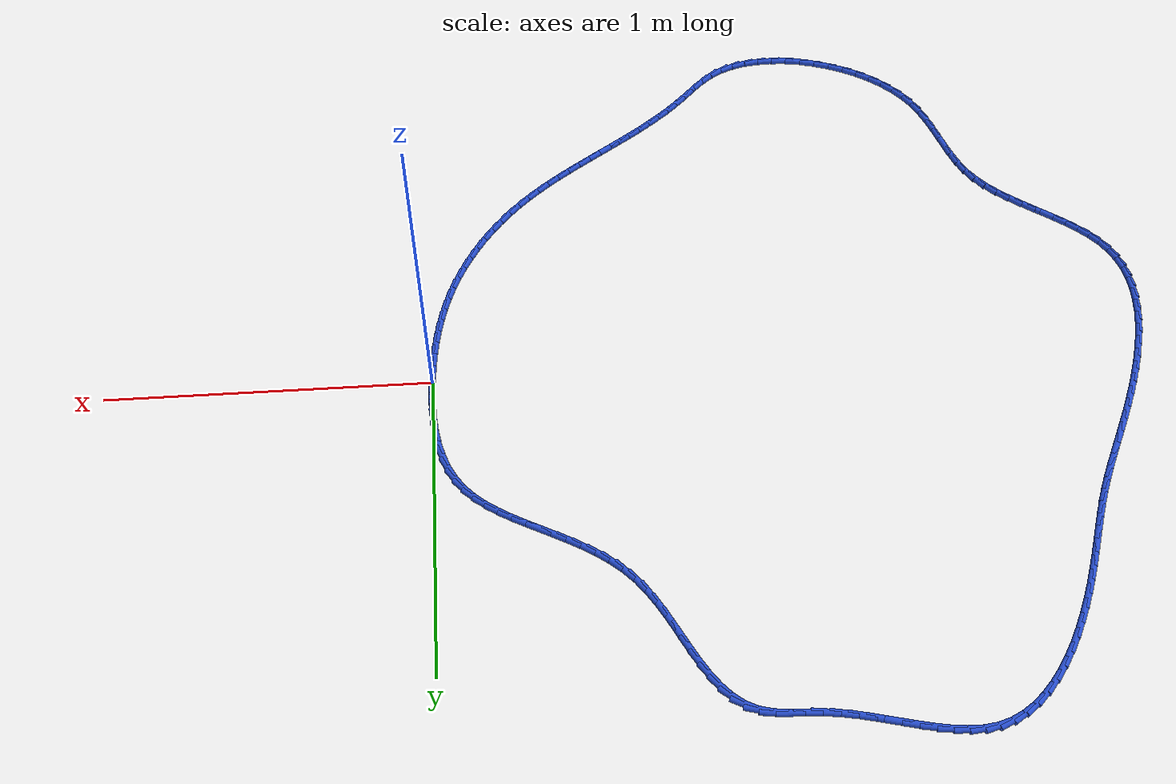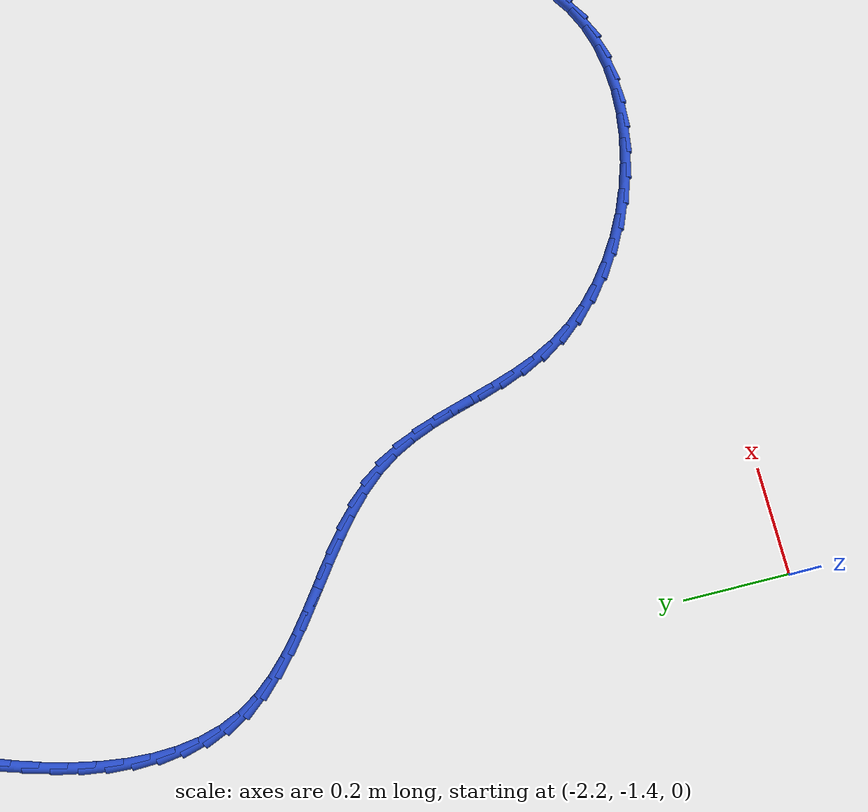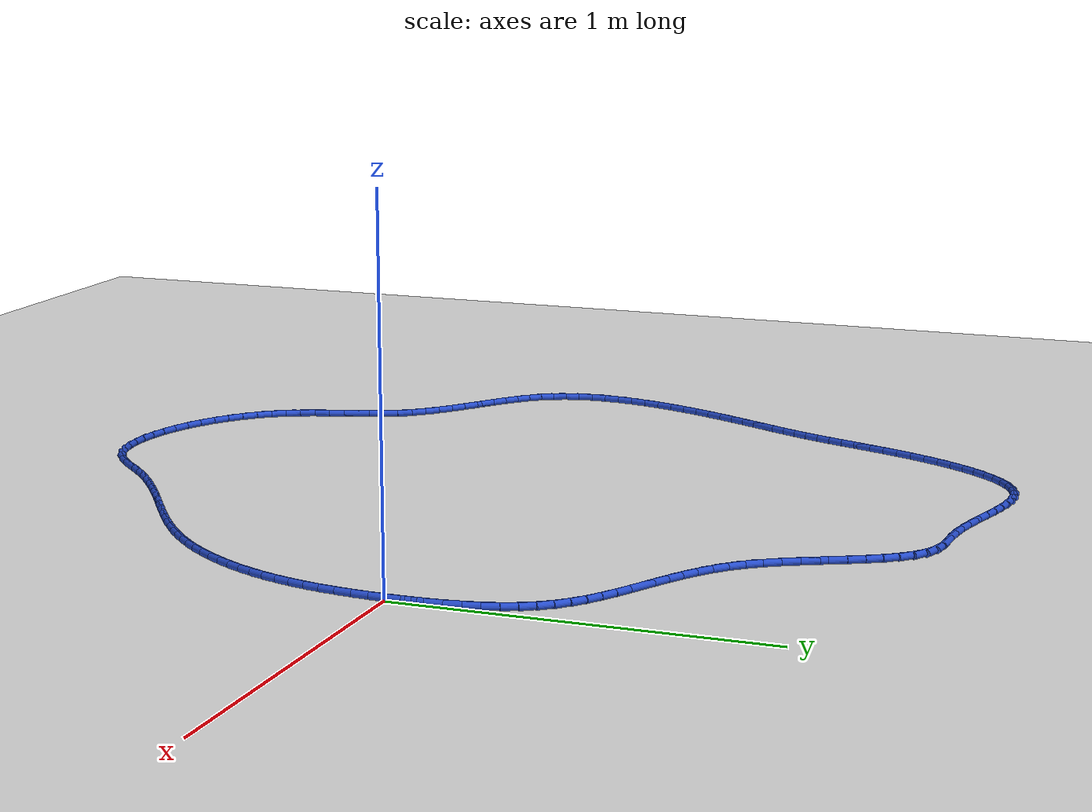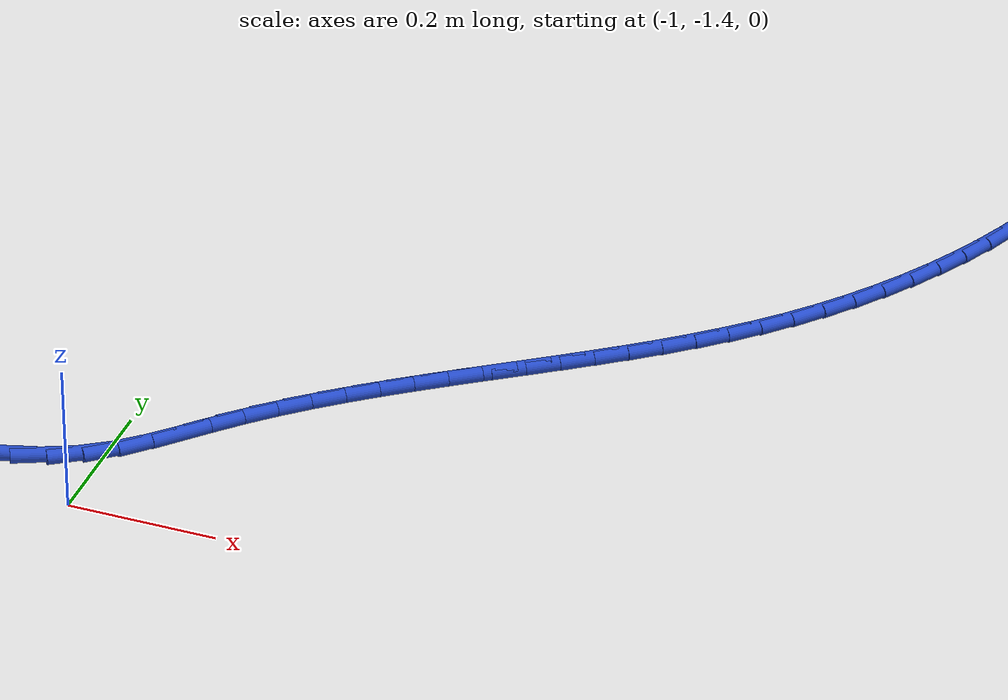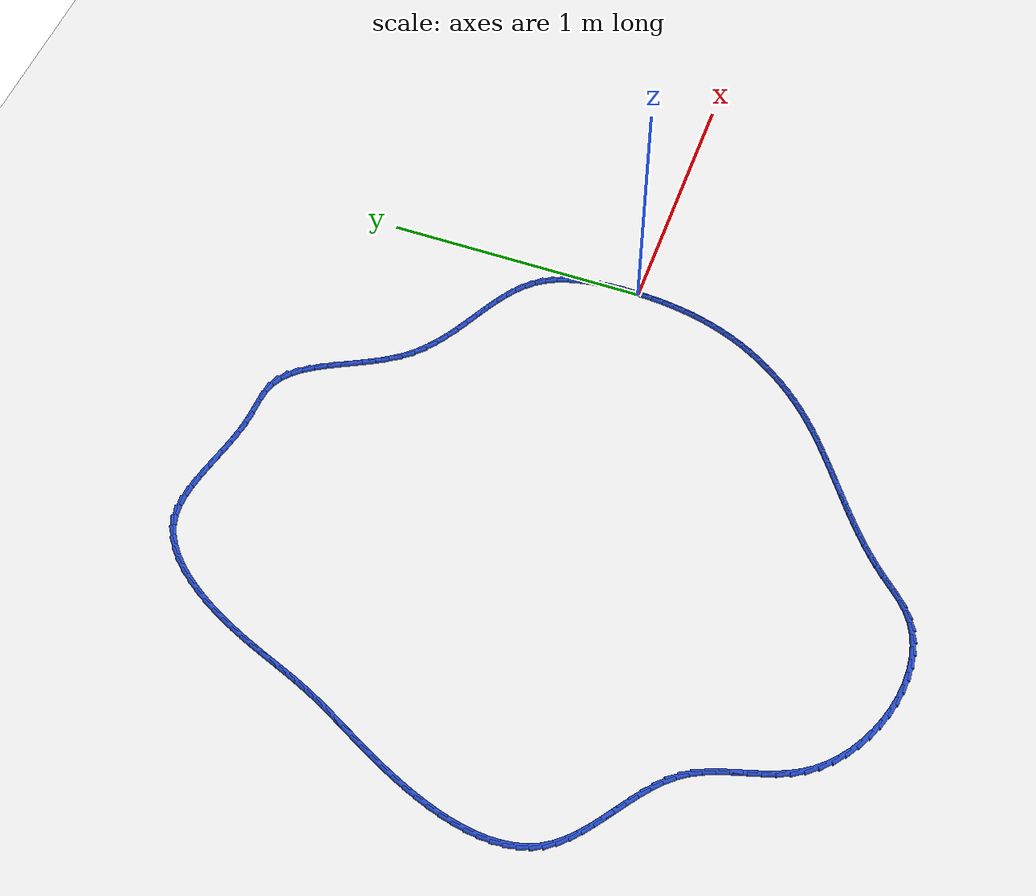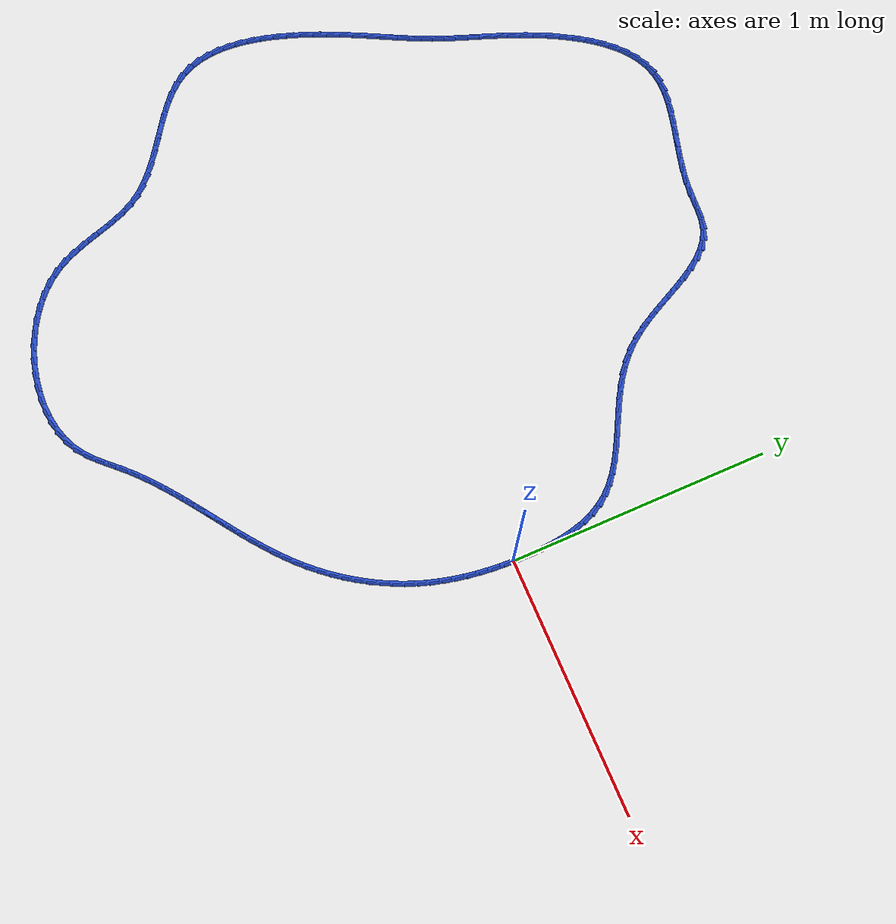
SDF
<sdf version="1.6">
 <world name="default">
  <light name="sun" type="directional">
   <pose>0 0 10 0 -0 0</pose>
   <diffuse>0.8 0.8 0.8 1</diffuse>
   <specular>0.2 0.2 0.2 1</specular>
   <attenuation>
    <range>1000</range>
    <constant>0.9</constant>
    <linear>0.01</linear>
    <quadratic>0.001</quadratic>
   </attenuation>
   <direction>-0.5 0.1 -0.9</direction>
  </light>
  <model name="ground_plane">
   <static>1</static>
   <link name="link">
    <collision name="collision">
     <geometry><plane><normal>0 0 1</normal><size>100 100</size></plane></geometry>
     <surface><friction><ode><mu>100</mu><mu2>50</mu2></ode></friction></surface>
    </collision>
    <visual name="visual">
     <cast_shadows>0</cast_shadows>
     <geometry><plane><normal>0 0 1</normal><size>100 100</size></plane></geometry>
     <material>
      <script><uri>file://media/materials/scripts/gazebo.material</uri><name>Gazebo/WhiteGlow</name></script>
     </material>
    </visual>
   </link>
  </model>
  <gravity>0 0 -9.8</gravity>
  <magnetic_field>6e-06 2.3e-05 -4.2e-05</magnetic_field>
  <atmosphere type="adiabatic"/>
  <physics name="default_physics" default="0" type="ode">
   <max_step_size>0.001</max_step_size>
   <real_time_factor>1</real_time_factor>
   <real_time_update_rate>1000</real_time_update_rate>
  </physics>
  <scene><ambient>0.4 0.4 0.4 1</ambient><background>0.7 0.7 0.7 1</background><shadows>1</shadows></scene>
  <spherical_coordinates>
   <surface_model>EARTH_WGS84</surface_model>
   <latitude_deg>0</latitude_deg>
   <longitude_deg>0</longitude_deg>
   <elevation>0</elevation>
   <heading_deg>0</heading_deg>
  </spherical_coordinates>
  <model name="line">
   <link name="link_0">
    <pose>-1.0842021724855044e-17 5.551115123125783e-17 0.01 0 1.57 1.5490282287377952</pose>
    <collision name="collision">
     <geometry><cylinder><radius>0.01</radius><length>0.08</length></cylinder></geometry>
    </collision>
    <visual name="visual">
     <material>
      <script><name>Gazebo/Blue</name><uri>file://media/materials/scripts/gazebo.material</uri></script>
     </material>
     <geometry><cylinder><radius>0.01</radius><length>0.08</length></cylinder></geometry>
    </visual>
   </link>
   <link name="link_1">
    <pose>0.0010495427795255891 0.048207105472479146 0.01 0 1.57 -1.5560355234855865</pose>
    <collision name="collision">
     <geometry><cylinder><radius>0.01</radius><length>0.08</length></cylinder></geometry>
    </collision>
    <visual name="visual">
     <material>
      <script><name>Gazebo/Blue</name><uri>file://media/materials/scripts/gazebo.material</uri></script>
     </material>
     <geometry><cylinder><radius>0.01</radius><length>0.08</length></cylinder></geometry>
    </visual>
   </link>
   <link name="link_2">
    <pose>0.00033367665949480174 0.09670135832526107 0.01 0 1.57 -1.511313021172945</pose>
    <collision name="collision">
     <geometry><cylinder><radius>0.01</radius><length>0.08</length></cylinder></geometry>
    </collision>
    <visual name="visual">
     <material>
      <script><name>Gazebo/Blue</name><uri>file://media/materials/scripts/gazebo.material</uri></script>
     </material>
     <geometry><cylinder><radius>0.01</radius><length>0.08</length></cylinder></geometry>
    </visual>
   </link>
   <link name="link_3">
    <pose>-0.002537949901108395 0.1449205834363719 0.01 0 1.57 -1.4569491067449036</pose>
    <collision name="collision">
     <geometry><cylinder><radius>0.01</radius><length>0.08</length></cylinder></geometry>
    </collision>
    <visual name="visual">
     <material>
      <script><name>Gazebo/Blue</name><uri>file://media/materials/scripts/gazebo.material</uri></script>
     </material>
     <geometry><cylinder><radius>0.01</radius><length>0.08</length></cylinder></geometry>
    </visual>
   </link>
   <link name="link_4">
    <pose>-0.007955688443300017 0.1923026056838376 0.01 0 1.57 -1.391075005947091</pose>
    <collision name="collision">
     <geometry><cylinder><radius>0.01</radius><length>0.08</length></cylinder></geometry>
    </collision>
    <visual name="visual">
     <material>
      <script><name>Gazebo/Blue</name><uri>file://media/materials/scripts/gazebo.material</uri></script>
     </material>
     <geometry><cylinder><radius>0.01</radius><length>0.08</length></cylinder></geometry>
    </visual>
   </link>
   <link name="link_5">
    <pose>-0.016309890508096093 0.2382852499456845 0.01 0 1.57 -1.3114231536452396</pose>
    <collision name="collision">
     <geometry><cylinder><radius>0.01</radius><length>0.08</length></cylinder></geometry>
    </collision>
    <visual name="visual">
     <material>
      <script><name>Gazebo/Blue</name><uri>file://media/materials/scripts/gazebo.material</uri></script>
     </material>
     <geometry><cylinder><radius>0.01</radius><length>0.08</length></cylinder></geometry>
    </visual>
   </link>
   <link name="link_6">
    <pose>-0.027990907636512657 0.28230634109993863 0.01 0 1.57 -1.2154807211104535</pose>
    <collision name="collision">
     <geometry><cylinder><radius>0.01</radius><length>0.08</length></cylinder></geometry>
    </collision>
    <visual name="visual">
     <material>
      <script><name>Gazebo/Blue</name><uri>file://media/materials/scripts/gazebo.material</uri></script>
     </material>
     <geometry><cylinder><radius>0.01</radius><length>0.08</length></cylinder></geometry>
    </visual>
   </link>
   <link name="link_7">
    <pose>-0.0433890913695657 0.32380370402462577 0.01 0 1.57 -1.1009206993615657</pose>
    <collision name="collision">
     <geometry><cylinder><radius>0.01</radius><length>0.08</length></cylinder></geometry>
    </collision>
    <visual name="visual">
     <material>
      <script><name>Gazebo/Blue</name><uri>file://media/materials/scripts/gazebo.material</uri></script>
     </material>
     <geometry><cylinder><radius>0.01</radius><length>0.08</length></cylinder></geometry>
    </visual>
   </link>
   <link name="link_8">
    <pose>-0.06289479324827127 0.3622151635977724 0.01 0 1.57 -0.9669472272853215</pose>
    <collision name="collision">
     <geometry><cylinder><radius>0.01</radius><length>0.08</length></cylinder></geometry>
    </collision>
    <visual name="visual">
     <material>
      <script><name>Gazebo/Blue</name><uri>file://media/materials/scripts/gazebo.material</uri></script>
     </material>
     <geometry><cylinder><radius>0.01</radius><length>0.08</length></cylinder></geometry>
    </visual>
   </link>
   <link name="link_9">
    <pose>-0.08688518394548424 0.39699380557234987 0.01 0 1.57 -0.830806303257848</pose>
    <collision name="collision">
     <geometry><cylinder><radius>0.01</radius><length>0.08</length></cylinder></geometry>
    </collision>
    <visual name="visual">
     <material>
      <script><name>Gazebo/Blue</name><uri>file://media/materials/scripts/gazebo.material</uri></script>
     </material>
     <geometry><cylinder><radius>0.01</radius><length>0.08</length></cylinder></geometry>
    </visual>
   </link>
   <link name="link_10">
    <pose>-0.1152934890398682 0.42810671754720275 0.01 0 1.57 -0.7161407465516259</pose>
    <collision name="collision">
     <geometry><cylinder><radius>0.01</radius><length>0.08</length></cylinder></geometry>
    </collision>
    <visual name="visual">
     <material>
      <script><name>Gazebo/Blue</name><uri>file://media/materials/scripts/gazebo.material</uri></script>
     </material>
     <geometry><cylinder><radius>0.01</radius><length>0.08</length></cylinder></geometry>
    </visual>
   </link>
   <link name="link_11">
    <pose>-0.14751298136062538 0.45614614710951507 0.01 0 1.57 -0.6261447471100968</pose>
    <collision name="collision">
     <geometry><cylinder><radius>0.01</radius><length>0.08</length></cylinder></geometry>
    </collision>
    <visual name="visual">
     <material>
      <script><name>Gazebo/Blue</name><uri>file://media/materials/scripts/gazebo.material</uri></script>
     </material>
     <geometry><cylinder><radius>0.01</radius><length>0.08</length></cylinder></geometry>
    </visual>
   </link>
   <link name="link_12">
    <pose>-0.18290432032476264 0.4817421018178898 0.01 0 1.57 -0.5601164094464074</pose>
    <collision name="collision">
     <geometry><cylinder><radius>0.01</radius><length>0.08</length></cylinder></geometry>
    </collision>
    <visual name="visual">
     <material>
      <script><name>Gazebo/Blue</name><uri>file://media/materials/scripts/gazebo.material</uri></script>
     </material>
     <geometry><cylinder><radius>0.01</radius><length>0.08</length></cylinder></geometry>
    </visual>
   </link>
   <link name="link_13">
    <pose>-0.22082816534928712 0.5055245892309298 0.01 0 1.57 -0.5162341635020862</pose>
    <collision name="collision">
     <geometry><cylinder><radius>0.01</radius><length>0.08</length></cylinder></geometry>
    </collision>
    <visual name="visual">
     <material>
      <script><name>Gazebo/Blue</name><uri>file://media/materials/scripts/gazebo.material</uri></script>
     </material>
     <geometry><cylinder><radius>0.01</radius><length>0.08</length></cylinder></geometry>
    </visual>
   </link>
   <link name="link_14">
    <pose>-0.26064517585120595 0.5281236169072386 0.01 0 1.57 -0.49262879492609823</pose>
    <collision name="collision">
     <geometry><cylinder><radius>0.01</radius><length>0.08</length></cylinder></geometry>
    </collision>
    <visual name="visual">
     <material>
      <script><name>Gazebo/Blue</name><uri>file://media/materials/scripts/gazebo.material</uri></script>
     </material>
     <geometry><cylinder><radius>0.01</radius><length>0.08</length></cylinder></geometry>
    </visual>
   </link>
   <link name="link_15">
    <pose>-0.3017160112475259 0.5501691924054191 0.01 0 1.57 -0.48789989019928315</pose>
    <collision name="collision">
     <geometry><cylinder><radius>0.01</radius><length>0.08</length></cylinder></geometry>
    </collision>
    <visual name="visual">
     <material>
      <script><name>Gazebo/Blue</name><uri>file://media/materials/scripts/gazebo.material</uri></script>
     </material>
     <geometry><cylinder><radius>0.01</radius><length>0.08</length></cylinder></geometry>
    </visual>
   </link>
   <link name="link_16">
    <pose>-0.34340133095525444 0.5722913232840745 0.01 0 1.57 -0.5012835122891918</pose>
    <collision name="collision">
     <geometry><cylinder><radius>0.01</radius><length>0.08</length></cylinder></geometry>
    </collision>
    <visual name="visual">
     <material>
      <script><name>Gazebo/Blue</name><uri>file://media/materials/scripts/gazebo.material</uri></script>
     </material>
     <geometry><cylinder><radius>0.01</radius><length>0.08</length></cylinder></geometry>
    </visual>
   </link>
   <link name="link_17">
    <pose>-0.3850617943913983 0.595120017101808 0.01 0 1.57 -0.5326263015260709</pose>
    <collision name="collision">
     <geometry><cylinder><radius>0.01</radius><length>0.08</length></cylinder></geometry>
    </collision>
    <visual name="visual">
     <material>
      <script><name>Gazebo/Blue</name><uri>file://media/materials/scripts/gazebo.material</uri></script>
     </material>
     <geometry><cylinder><radius>0.01</radius><length>0.08</length></cylinder></geometry>
    </visual>
   </link>
   <link name="link_18">
    <pose>-0.4260580609729646 0.6192852814172226 0.01 0 1.57 -0.5822251473659691</pose>
    <collision name="collision">
     <geometry><cylinder><radius>0.01</radius><length>0.08</length></cylinder></geometry>
    </collision>
    <visual name="visual">
     <material>
      <script><name>Gazebo/Blue</name><uri>file://media/materials/scripts/gazebo.material</uri></script>
     </material>
     <geometry><cylinder><radius>0.01</radius><length>0.08</length></cylinder></geometry>
    </visual>
   </link>
   <link name="link_19">
    <pose>-0.4657507901169604 0.6454171237889215 0.01 0 1.57 -0.6505172921722611</pose>
    <collision name="collision">
     <geometry><cylinder><radius>0.01</radius><length>0.08</length></cylinder></geometry>
    </collision>
    <visual name="visual">
     <material>
      <script><name>Gazebo/Blue</name><uri>file://media/materials/scripts/gazebo.material</uri></script>
     </material>
     <geometry><cylinder><radius>0.01</radius><length>0.08</length></cylinder></geometry>
    </visual>
   </link>
   <link name="link_20">
    <pose>-0.5035006412403927 0.6741455517755077 0.01 0 1.57 -0.7375728547880904</pose>
    <collision name="collision">
     <geometry><cylinder><radius>0.01</radius><length>0.08</length></cylinder></geometry>
    </collision>
    <visual name="visual">
     <material>
      <script><name>Gazebo/Blue</name><uri>file://media/materials/scripts/gazebo.material</uri></script>
     </material>
     <geometry><cylinder><radius>0.01</radius><length>0.08</length></cylinder></geometry>
    </visual>
   </link>
   <link name="link_21">
    <pose>-0.5386682737602687 0.7061005729355847 0.01 0 1.57 -0.8422299888736215</pose>
    <collision name="collision">
     <geometry><cylinder><radius>0.01</radius><length>0.08</length></cylinder></geometry>
    </collision>
    <visual name="visual">
     <material>
      <script><name>Gazebo/Blue</name><uri>file://media/materials/scripts/gazebo.material</uri></script>
     </material>
     <geometry><cylinder><radius>0.01</radius><length>0.08</length></cylinder></geometry>
    </visual>
   </link>
   <link name="link_22">
    <pose>-0.5706190970001618 0.7419062742838919 0.01 0 1.57 -0.9472401490970578</pose>
    <collision name="collision">
     <geometry><cylinder><radius>0.01</radius><length>0.08</length></cylinder></geometry>
    </collision>
    <visual name="visual">
     <material>
      <script><name>Gazebo/Blue</name><uri>file://media/materials/scripts/gazebo.material</uri></script>
     </material>
     <geometry><cylinder><radius>0.01</radius><length>0.08</length></cylinder></geometry>
    </visual>
   </link>
   <link name="link_23">
    <pose>-0.5991793371293498 0.7816123554636321 0.01 0 1.57 -1.0257406184039257</pose>
    <collision name="collision">
     <geometry><cylinder><radius>0.01</radius><length>0.08</length></cylinder></geometry>
    </collision>
    <visual name="visual">
     <material>
      <script><name>Gazebo/Blue</name><uri>file://media/materials/scripts/gazebo.material</uri></script>
     </material>
     <geometry><cylinder><radius>0.01</radius><length>0.08</length></cylinder></geometry>
    </visual>
   </link>
   <link name="link_24">
    <pose>-0.6250146577777984 0.8242221952616594 0.01 0 1.57 -1.0776527280225738</pose>
    <collision name="collision">
     <geometry><cylinder><radius>0.01</radius><length>0.08</length></cylinder></geometry>
    </collision>
    <visual name="visual">
     <material>
      <script><name>Gazebo/Blue</name><uri>file://media/materials/scripts/gazebo.material</uri></script>
     </material>
     <geometry><cylinder><radius>0.01</radius><length>0.08</length></cylinder></geometry>
    </visual>
   </link>
   <link name="link_25">
    <pose>-0.6488798445549542 0.8686280859452784 0.01 0 1.57 -1.1053280331876434</pose>
    <collision name="collision">
     <geometry><cylinder><radius>0.01</radius><length>0.08</length></cylinder></geometry>
    </collision>
    <visual name="visual">
     <material>
      <script><name>Gazebo/Blue</name><uri>file://media/materials/scripts/gazebo.material</uri></script>
     </material>
     <geometry><cylinder><radius>0.01</radius><length>0.08</length></cylinder></geometry>
    </visual>
   </link>
   <link name="link_26">
    <pose>-0.6715296830702626 0.9137223197817932 0.01 0 1.57 -1.1098053383089606</pose>
    <collision name="collision">
     <geometry><cylinder><radius>0.01</radius><length>0.08</length></cylinder></geometry>
    </collision>
    <visual name="visual">
     <material>
      <script><name>Gazebo/Blue</name><uri>file://media/materials/scripts/gazebo.material</uri></script>
     </material>
     <geometry><cylinder><radius>0.01</radius><length>0.08</length></cylinder></geometry>
    </visual>
   </link>
   <link name="link_27">
    <pose>-0.6937189589331698 0.9583971890385086 0.01 0 1.57 -1.0904264683494893</pose>
    <collision name="collision">
     <geometry><cylinder><radius>0.01</radius><length>0.08</length></cylinder></geometry>
    </collision>
    <visual name="visual">
     <material>
      <script><name>Gazebo/Blue</name><uri>file://media/materials/scripts/gazebo.material</uri></script>
     </material>
     <geometry><cylinder><radius>0.01</radius><length>0.08</length></cylinder></geometry>
    </visual>
   </link>
   <link name="link_28">
    <pose>-0.7162024577531219 1.0015449859827283 0.01 0 1.57 -1.0445671053917676</pose>
    <collision name="collision">
     <geometry><cylinder><radius>0.01</radius><length>0.08</length></cylinder></geometry>
    </collision>
    <visual name="visual">
     <material>
      <script><name>Gazebo/Blue</name><uri>file://media/materials/scripts/gazebo.material</uri></script>
     </material>
     <geometry><cylinder><radius>0.01</radius><length>0.08</length></cylinder></geometry>
    </visual>
   </link>
   <link name="link_29">
    <pose>-0.7397349651395644 1.0420580028817565 0.01 0 1.57 -0.9674651798101187</pose>
    <collision name="collision">
     <geometry><cylinder><radius>0.01</radius><length>0.08</length></cylinder></geometry>
    </collision>
    <visual name="visual">
     <material>
      <script><name>Gazebo/Blue</name><uri>file://media/materials/scripts/gazebo.material</uri></script>
     </material>
     <geometry><cylinder><radius>0.01</radius><length>0.08</length></cylinder></geometry>
    </visual>
   </link>
   <link name="link_30">
    <pose>-0.7650712667019435 1.0788285320028979 0.01 0 1.57 -0.8525949724966555</pose>
    <collision name="collision">
     <geometry><cylinder><radius>0.01</radius><length>0.08</length></cylinder></geometry>
    </collision>
    <visual name="visual">
     <material>
      <script><name>Gazebo/Blue</name><uri>file://media/materials/scripts/gazebo.material</uri></script>
     </material>
     <geometry><cylinder><radius>0.01</radius><length>0.08</length></cylinder></geometry>
    </visual>
   </link>
   <link name="link_31">
    <pose>-0.7929661480497051 1.1107488656134565 0.01 0 1.57 -0.6938972679533626</pose>
    <collision name="collision">
     <geometry><cylinder><radius>0.01</radius><length>0.08</length></cylinder></geometry>
    </collision>
    <visual name="visual">
     <material>
      <script><name>Gazebo/Blue</name><uri>file://media/materials/scripts/gazebo.material</uri></script>
     </material>
     <geometry><cylinder><radius>0.01</radius><length>0.08</length></cylinder></geometry>
    </visual>
   </link>
   <link name="link_32">
    <pose>-0.8241743947922953 1.1367112959807364 0.01 0 1.57 -0.49178162447629625</pose>
    <collision name="collision">
     <geometry><cylinder><radius>0.01</radius><length>0.08</length></cylinder></geometry>
    </collision>
    <visual name="visual">
     <material>
      <script><name>Gazebo/Blue</name><uri>file://media/materials/scripts/gazebo.material</uri></script>
     </material>
     <geometry><cylinder><radius>0.01</radius><length>0.08</length></cylinder></geometry>
    </visual>
   </link>
   <link name="link_33">
    <pose>-0.8594507925391599 1.1556081153720426 0.01 0 1.57 -0.26612469337725114</pose>
    <collision name="collision">
     <geometry><cylinder><radius>0.01</radius><length>0.08</length></cylinder></geometry>
    </collision>
    <visual name="visual">
     <material>
      <script><name>Gazebo/Blue</name><uri>file://media/materials/scripts/gazebo.material</uri></script>
     </material>
     <geometry><cylinder><radius>0.01</radius><length>0.08</length></cylinder></geometry>
    </visual>
   </link>
   <link name="link_34">
    <pose>-0.8994639942203072 1.1665153319827022 0.01 0 1.57 -0.10421338723054308</pose>
    <collision name="collision">
     <geometry><cylinder><radius>0.01</radius><length>0.08</length></cylinder></geometry>
    </collision>
    <visual name="visual">
     <material>
      <script><name>Gazebo/Blue</name><uri>file://media/materials/scripts/gazebo.material</uri></script>
     </material>
     <geometry><cylinder><radius>0.01</radius><length>0.08</length></cylinder></geometry>
    </visual>
   </link>
   <link name="link_35">
    <pose>-0.9436505728215254 1.1711369079023373 0.01 0 1.57 -0.04269838373388305</pose>
    <collision name="collision">
     <geometry><cylinder><radius>0.01</radius><length>0.08</length></cylinder></geometry>
    </collision>
    <visual name="visual">
     <material>
      <script><name>Gazebo/Blue</name><uri>file://media/materials/scripts/gazebo.material</uri></script>
     </material>
     <geometry><cylinder><radius>0.01</radius><length>0.08</length></cylinder></geometry>
    </visual>
   </link>
   <link name="link_36">
    <pose>-0.9905268410954139 1.17313966605189 0.01 0 1.57 -0.06424378131988522</pose>
    <collision name="collision">
     <geometry><cylinder><radius>0.01</radius><length>0.08</length></cylinder></geometry>
    </collision>
    <visual name="visual">
     <material>
      <script><name>Gazebo/Blue</name><uri>file://media/materials/scripts/gazebo.material</uri></script>
     </material>
     <geometry><cylinder><radius>0.01</radius><length>0.08</length></cylinder></geometry>
    </visual>
   </link>
   <link name="link_37">
    <pose>-1.0385887066114408 1.1762315969385748 0.01 0 1.57 -0.13547735031653296</pose>
    <collision name="collision">
     <geometry><cylinder><radius>0.01</radius><length>0.08</length></cylinder></geometry>
    </collision>
    <visual name="visual">
     <material>
      <script><name>Gazebo/Blue</name><uri>file://media/materials/scripts/gazebo.material</uri></script>
     </material>
     <geometry><cylinder><radius>0.01</radius><length>0.08</length></cylinder></geometry>
    </visual>
   </link>
   <link name="link_38">
    <pose>-1.0867094646149853 1.1827910498977499 0.01 0 1.57 -0.1938952540323659</pose>
    <collision name="collision">
     <geometry><cylinder><radius>0.01</radius><length>0.08</length></cylinder></geometry>
    </collision>
    <visual name="visual">
     <material>
      <script><name>Gazebo/Blue</name><uri>file://media/materials/scripts/gazebo.material</uri></script>
     </material>
     <geometry><cylinder><radius>0.01</radius><length>0.08</length></cylinder></geometry>
    </visual>
   </link>
   <link name="link_39">
    <pose>-1.134613542390609 1.1921976006581778 0.01 0 1.57 -0.231873636968326</pose>
    <collision name="collision">
     <geometry><cylinder><radius>0.01</radius><length>0.08</length></cylinder></geometry>
    </collision>
    <visual name="visual">
     <material>
      <script><name>Gazebo/Blue</name><uri>file://media/materials/scripts/gazebo.material</uri></script>
     </material>
     <geometry><cylinder><radius>0.01</radius><length>0.08</length></cylinder></geometry>
    </visual>
   </link>
   <link name="link_40">
    <pose>-1.1821419594120144 1.2034200384155798 0.01 0 1.57 -0.25015247729503914</pose>
    <collision name="collision">
     <geometry><cylinder><radius>0.01</radius><length>0.08</length></cylinder></geometry>
    </collision>
    <visual name="visual">
     <material>
      <script><name>Gazebo/Blue</name><uri>file://media/materials/scripts/gazebo.material</uri></script>
     </material>
     <geometry><cylinder><radius>0.01</radius><length>0.08</length></cylinder></geometry>
    </visual>
   </link>
   <link name="link_41">
    <pose>-1.2291357351529062 1.2154271523656763 0.01 0 1.57 -0.24874671453014993</pose>
    <collision name="collision">
     <geometry><cylinder><radius>0.01</radius><length>0.08</length></cylinder></geometry>
    </collision>
    <visual name="visual">
     <material>
      <script><name>Gazebo/Blue</name><uri>file://media/materials/scripts/gazebo.material</uri></script>
     </material>
     <geometry><cylinder><radius>0.01</radius><length>0.08</length></cylinder></geometry>
    </visual>
   </link>
   <link name="link_42">
    <pose>-1.275435889086986 1.2271877317041868 0.01 0 1.57 -0.22669308341764077</pose>
    <collision name="collision">
     <geometry><cylinder><radius>0.01</radius><length>0.08</length></cylinder></geometry>
    </collision>
    <visual name="visual">
     <material>
      <script><name>Gazebo/Blue</name><uri>file://media/materials/scripts/gazebo.material</uri></script>
     </material>
     <geometry><cylinder><radius>0.01</radius><length>0.08</length></cylinder></geometry>
    </visual>
   </link>
   <link name="link_43">
    <pose>-1.3208834406879577 1.2376705656268328 0.01 0 1.57 -0.1819137380299662</pose>
    <collision name="collision">
     <geometry><cylinder><radius>0.01</radius><length>0.08</length></cylinder></geometry>
    </collision>
    <visual name="visual">
     <material>
      <script><name>Gazebo/Blue</name><uri>file://media/materials/scripts/gazebo.material</uri></script>
     </material>
     <geometry><cylinder><radius>0.01</radius><length>0.08</length></cylinder></geometry>
    </visual>
   </link>
   <link name="link_44">
    <pose>-1.3653194094295258 1.2458444433293347 0.01 0 1.57 -0.11126091782519251</pose>
    <collision name="collision">
     <geometry><cylinder><radius>0.01</radius><length>0.08</length></cylinder></geometry>
    </collision>
    <visual name="visual">
     <material>
      <script><name>Gazebo/Blue</name><uri>file://media/materials/scripts/gazebo.material</uri></script>
     </material>
     <geometry><cylinder><radius>0.01</radius><length>0.08</length></cylinder></geometry>
    </visual>
   </link>
   <link name="link_45">
    <pose>-1.4085848147853914 1.2506781540074126 0.01 0 1.57 -0.011024314354179412</pose>
    <collision name="collision">
     <geometry><cylinder><radius>0.01</radius><length>0.08</length></cylinder></geometry>
    </collision>
    <visual name="visual">
     <material>
      <script><name>Gazebo/Blue</name><uri>file://media/materials/scripts/gazebo.material</uri></script>
     </material>
     <geometry><cylinder><radius>0.01</radius><length>0.08</length></cylinder></geometry>
    </visual>
   </link>
   <link name="link_46">
    <pose>-1.45052067622926 1.2511404868567872 0.01 0 1.57 0.12153844991575335</pose>
    <collision name="collision">
     <geometry><cylinder><radius>0.01</radius><length>0.08</length></cylinder></geometry>
    </collision>
    <visual name="visual">
     <material>
      <script><name>Gazebo/Blue</name><uri>file://media/materials/scripts/gazebo.material</uri></script>
     </material>
     <geometry><cylinder><radius>0.01</radius><length>0.08</length></cylinder></geometry>
    </visual>
   </link>
   <link name="link_47">
    <pose>-1.4909680132348333 1.2462002310731795 0.01 0 1.57 0.28374294347376755</pose>
    <collision name="collision">
     <geometry><cylinder><radius>0.01</radius><length>0.08</length></cylinder></geometry>
    </collision>
    <visual name="visual">
     <material>
      <script><name>Gazebo/Blue</name><uri>file://media/materials/scripts/gazebo.material</uri></script>
     </material>
     <geometry><cylinder><radius>0.01</radius><length>0.08</length></cylinder></geometry>
    </visual>
   </link>
   <link name="link_48">
    <pose>-1.5297729824271022 1.2348842694154576 0.01 0 1.57 0.4464500116357379</pose>
    <collision name="collision">
     <geometry><cylinder><radius>0.01</radius><length>0.08</length></cylinder></geometry>
    </collision>
    <visual name="visual">
     <material>
      <script><name>Gazebo/Blue</name><uri>file://media/materials/scripts/gazebo.material</uri></script>
     </material>
     <geometry><cylinder><radius>0.01</radius><length>0.08</length></cylinder></geometry>
    </visual>
   </link>
   <link name="link_49">
    <pose>-1.5668622750144519 1.2171302113556084 0.01 0 1.57 0.587130415299889</pose>
    <collision name="collision">
     <geometry><cylinder><radius>0.01</radius><length>0.08</length></cylinder></geometry>
    </collision>
    <visual name="visual">
     <material>
      <script><name>Gazebo/Blue</name><uri>file://media/materials/scripts/gazebo.material</uri></script>
     </material>
     <geometry><cylinder><radius>0.01</radius><length>0.08</length></cylinder></geometry>
    </visual>
   </link>
   <link name="link_50">
    <pose>-1.6022265088916494 1.1935985823914308 0.01 0 1.57 0.7052177996515869</pose>
    <collision name="collision">
     <geometry><cylinder><radius>0.01</radius><length>0.08</length></cylinder></geometry>
    </collision>
    <visual name="visual">
     <material>
      <script><name>Gazebo/Blue</name><uri>file://media/materials/scripts/gazebo.material</uri></script>
     </material>
     <geometry><cylinder><radius>0.01</radius><length>0.08</length></cylinder></geometry>
    </visual>
   </link>
   <link name="link_51">
    <pose>-1.6358580618890879 1.1649698102828205 0.01 0 1.57 0.8031710921837236</pose>
    <collision name="collision">
     <geometry><cylinder><radius>0.01</radius><length>0.08</length></cylinder></geometry>
    </collision>
    <visual name="visual">
     <material>
      <script><name>Gazebo/Blue</name><uri>file://media/materials/scripts/gazebo.material</uri></script>
     </material>
     <geometry><cylinder><radius>0.01</radius><length>0.08</length></cylinder></geometry>
    </visual>
   </link>
   <link name="link_52">
    <pose>-1.667749311837157 1.131924322789673 0.01 0 1.57 0.8842669870918348</pose>
    <collision name="collision">
     <geometry><cylinder><radius>0.01</radius><length>0.08</length></cylinder></geometry>
    </collision>
    <visual name="visual">
     <material>
      <script><name>Gazebo/Blue</name><uri>file://media/materials/scripts/gazebo.material</uri></script>
     </material>
     <geometry><cylinder><radius>0.01</radius><length>0.08</length></cylinder></geometry>
    </visual>
   </link>
   <link name="link_53">
    <pose>-1.6978926365662494 1.0951425476718832 0.01 0 1.57 0.9516726267059107</pose>
    <collision name="collision">
     <geometry><cylinder><radius>0.01</radius><length>0.08</length></cylinder></geometry>
    </collision>
    <visual name="visual">
     <material>
      <script><name>Gazebo/Blue</name><uri>file://media/materials/scripts/gazebo.material</uri></script>
     </material>
     <geometry><cylinder><radius>0.01</radius><length>0.08</length></cylinder></geometry>
    </visual>
   </link>
   <link name="link_54">
    <pose>-1.7262804139067571 1.0553049126893481 0.01 0 1.57 1.0080946264466348</pose>
    <collision name="collision">
     <geometry><cylinder><radius>0.01</radius><length>0.08</length></cylinder></geometry>
    </collision>
    <visual name="visual">
     <material>
      <script><name>Gazebo/Blue</name><uri>file://media/materials/scripts/gazebo.material</uri></script>
     </material>
     <geometry><cylinder><radius>0.01</radius><length>0.08</length></cylinder></geometry>
    </visual>
   </link>
   <link name="link_55">
    <pose>-1.7529050216890711 1.0130918456019617 0.01 0 1.57 1.0557202202327656</pose>
    <collision name="collision">
     <geometry><cylinder><radius>0.01</radius><length>0.08</length></cylinder></geometry>
    </collision>
    <visual name="visual">
     <material>
      <script><name>Gazebo/Blue</name><uri>file://media/materials/scripts/gazebo.material</uri></script>
     </material>
     <geometry><cylinder><radius>0.01</radius><length>0.08</length></cylinder></geometry>
    </visual>
   </link>
   <link name="link_56">
    <pose>-1.7777588377435833 0.9691837741696199 0.01 0 1.57 1.0962728740174488</pose>
    <collision name="collision">
     <geometry><cylinder><radius>0.01</radius><length>0.08</length></cylinder></geometry>
    </collision>
    <visual name="visual">
     <material>
      <script><name>Gazebo/Blue</name><uri>file://media/materials/scripts/gazebo.material</uri></script>
     </material>
     <geometry><cylinder><radius>0.01</radius><length>0.08</length></cylinder></geometry>
    </visual>
   </link>
   <link name="link_57">
    <pose>-1.8008342399006858 0.9242611261522187 0.01 0 1.57 1.1310975707498057</pose>
    <collision name="collision">
     <geometry><cylinder><radius>0.01</radius><length>0.08</length></cylinder></geometry>
    </collision>
    <visual name="visual">
     <material>
      <script><name>Gazebo/Blue</name><uri>file://media/materials/scripts/gazebo.material</uri></script>
     </material>
     <geometry><cylinder><radius>0.01</radius><length>0.08</length></cylinder></geometry>
    </visual>
   </link>
   <link name="link_58">
    <pose>-1.82212360599077 0.8790043293096529 0.01 0 1.57 1.1612116730305337</pose>
    <collision name="collision">
     <geometry><cylinder><radius>0.01</radius><length>0.08</length></cylinder></geometry>
    </collision>
    <visual name="visual">
     <material>
      <script><name>Gazebo/Blue</name><uri>file://media/materials/scripts/gazebo.material</uri></script>
     </material>
     <geometry><cylinder><radius>0.01</radius><length>0.08</length></cylinder></geometry>
    </visual>
   </link>
   <link name="link_59">
    <pose>-1.841625740555175 0.834082766076162 0.01 0 1.57 1.1863079842871744</pose>
    <collision name="collision">
     <geometry><cylinder><radius>0.01</radius><length>0.08</length></cylinder></geometry>
    </collision>
    <visual name="visual">
     <material>
      <script><name>Gazebo/Blue</name><uri>file://media/materials/scripts/gazebo.material</uri></script>
     </material>
     <geometry><cylinder><radius>0.01</radius><length>0.08</length></cylinder></geometry>
    </visual>
   </link>
   <link name="link_60">
    <pose>-1.8595241318148423 0.789848410587831 0.01 0 1.57 1.204922085759529</pose>
    <collision name="collision">
     <geometry><cylinder><radius>0.01</radius><length>0.08</length></cylinder></geometry>
    </collision>
    <visual name="visual">
     <material>
      <script><name>Gazebo/Blue</name><uri>file://media/materials/scripts/gazebo.material</uri></script>
     </material>
     <geometry><cylinder><radius>0.01</radius><length>0.08</length></cylinder></geometry>
    </visual>
   </link>
   <link name="link_61">
    <pose>-1.8762101031161145 0.7462960392381348 0.01 0 1.57 1.2163152799633052</pose>
    <collision name="collision">
     <geometry><cylinder><radius>0.01</radius><length>0.08</length></cylinder></geometry>
    </collision>
    <visual name="visual">
     <material>
      <script><name>Gazebo/Blue</name><uri>file://media/materials/scripts/gazebo.material</uri></script>
     </material>
     <geometry><cylinder><radius>0.01</radius><length>0.08</length></cylinder></geometry>
    </visual>
   </link>
   <link name="link_62">
    <pose>-1.8920860550599907 0.7034013903953374 0.01 0 1.57 1.2199239105358493</pose>
    <collision name="collision">
     <geometry><cylinder><radius>0.01</radius><length>0.08</length></cylinder></geometry>
    </collision>
    <visual name="visual">
     <material>
      <script><name>Gazebo/Blue</name><uri>file://media/materials/scripts/gazebo.material</uri></script>
     </material>
     <geometry><cylinder><radius>0.01</radius><length>0.08</length></cylinder></geometry>
    </visual>
   </link>
   <link name="link_63">
    <pose>-1.9075543882474701 0.6611402024277003 0.01 0 1.57 1.215321294217885</pose>
    <collision name="collision">
     <geometry><cylinder><radius>0.01</radius><length>0.08</length></cylinder></geometry>
    </collision>
    <visual name="visual">
     <material>
      <script><name>Gazebo/Blue</name><uri>file://media/materials/scripts/gazebo.material</uri></script>
     </material>
     <geometry><cylinder><radius>0.01</radius><length>0.08</length></cylinder></geometry>
    </visual>
   </link>
   <link name="link_64">
    <pose>-1.9230175032795513 0.619488213703487 0.01 0 1.57 1.202238526469194</pose>
    <collision name="collision">
     <geometry><cylinder><radius>0.01</radius><length>0.08</length></cylinder></geometry>
    </collision>
    <visual name="visual">
     <material>
      <script><name>Gazebo/Blue</name><uri>file://media/materials/scripts/gazebo.material</uri></script>
     </material>
     <geometry><cylinder><radius>0.01</radius><length>0.08</length></cylinder></geometry>
    </visual>
   </link>
   <link name="link_65">
    <pose>-1.938877800757235 0.5784211625909597 0.01 0 1.57 1.1805949535204254</pose>
    <collision name="collision">
     <geometry><cylinder><radius>0.01</radius><length>0.08</length></cylinder></geometry>
    </collision>
    <visual name="visual">
     <material>
      <script><name>Gazebo/Blue</name><uri>file://media/materials/scripts/gazebo.material</uri></script>
     </material>
     <geometry><cylinder><radius>0.01</radius><length>0.08</length></cylinder></geometry>
    </visual>
   </link>
   <link name="link_66">
    <pose>-1.9555376812815186 0.5379147874583806 0.01 0 1.57 1.1522814875554181</pose>
    <collision name="collision">
     <geometry><cylinder><radius>0.01</radius><length>0.08</length></cylinder></geometry>
    </collision>
    <visual name="visual">
     <material>
      <script><name>Gazebo/Blue</name><uri>file://media/materials/scripts/gazebo.material</uri></script>
     </material>
     <geometry><cylinder><radius>0.01</radius><length>0.08</length></cylinder></geometry>
    </visual>
   </link>
   <link name="link_67">
    <pose>-1.9733304780825713 0.49791231112431666 0.01 0 1.57 1.127555800034284</pose>
    <collision name="collision">
     <geometry><cylinder><radius>0.01</radius><length>0.08</length></cylinder></geometry>
    </collision>
    <visual name="visual">
     <material>
      <script><name>Gazebo/Blue</name><uri>file://media/materials/scripts/gazebo.material</uri></script>
     </material>
     <geometry><cylinder><radius>0.01</radius><length>0.08</length></cylinder></geometry>
    </visual>
   </link>
   <link name="link_68">
    <pose>-1.9921969406802522 0.45817213577511434 0.01 0 1.57 1.1101692776403407</pose>
    <collision name="collision">
     <geometry><cylinder><radius>0.01</radius><length>0.08</length></cylinder></geometry>
    </collision>
    <visual name="visual">
     <material>
      <script><name>Gazebo/Blue</name><uri>file://media/materials/scripts/gazebo.material</uri></script>
     </material>
     <geometry><cylinder><radius>0.01</radius><length>0.08</length></cylinder></geometry>
    </visual>
   </link>
   <link name="link_69">
    <pose>-2.011939294908904 0.41838744939066885 0.01 0 1.57 1.1001518261996726</pose>
    <collision name="collision">
     <geometry><cylinder><radius>0.01</radius><length>0.08</length></cylinder></geometry>
    </collision>
    <visual name="visual">
     <material>
      <script><name>Gazebo/Blue</name><uri>file://media/materials/scripts/gazebo.material</uri></script>
     </material>
     <geometry><cylinder><radius>0.01</radius><length>0.08</length></cylinder></geometry>
    </visual>
   </link>
   <link name="link_70">
    <pose>-2.032359609537484 0.37825136600760256 0.01 0 1.57 1.0973302186261464</pose>
    <collision name="collision">
     <geometry><cylinder><radius>0.01</radius><length>0.08</length></cylinder></geometry>
    </collision>
    <visual name="visual">
     <material>
      <script><name>Gazebo/Blue</name><uri>file://media/materials/scripts/gazebo.material</uri></script>
     </material>
     <geometry><cylinder><radius>0.01</radius><length>0.08</length></cylinder></geometry>
    </visual>
   </link>
   <link name="link_71">
    <pose>-2.053259953334948 0.3374569996625369 0.01 0 1.57 1.1013671255129809</pose>
    <collision name="collision">
     <geometry><cylinder><radius>0.01</radius><length>0.08</length></cylinder></geometry>
    </collision>
    <visual name="visual">
     <material>
      <script><name>Gazebo/Blue</name><uri>file://media/materials/scripts/gazebo.material</uri></script>
     </material>
     <geometry><cylinder><radius>0.01</radius><length>0.08</length></cylinder></geometry>
    </visual>
   </link>
   <link name="link_72">
    <pose>-2.0744423950702515 0.29569746439209443 0.01 0 1.57 1.1117920670356571</pose>
    <collision name="collision">
     <geometry><cylinder><radius>0.01</radius><length>0.08</length></cylinder></geometry>
    </collision>
    <visual name="visual">
     <material>
      <script><name>Gazebo/Blue</name><uri>file://media/materials/scripts/gazebo.material</uri></script>
     </material>
     <geometry><cylinder><radius>0.01</radius><length>0.08</length></cylinder></geometry>
    </visual>
   </link>
   <link name="link_73">
    <pose>-2.09570900351235 0.2526658742328966 0.01 0 1.57 1.127854771322869</pose>
    <collision name="collision">
     <geometry><cylinder><radius>0.01</radius><length>0.08</length></cylinder></geometry>
    </collision>
    <visual name="visual">
     <material>
      <script><name>Gazebo/Blue</name><uri>file://media/materials/scripts/gazebo.material</uri></script>
     </material>
     <geometry><cylinder><radius>0.01</radius><length>0.08</length></cylinder></geometry>
    </visual>
   </link>
   <link name="link_74">
    <pose>-2.1168410883079134 0.20811903797740663 0.01 0 1.57 1.1481061909104637</pose>
    <collision name="collision">
     <geometry><cylinder><radius>0.01</radius><length>0.08</length></cylinder></geometry>
    </collision>
    <visual name="visual">
     <material>
      <script><name>Gazebo/Blue</name><uri>file://media/materials/scripts/gazebo.material</uri></script>
     </material>
     <geometry><cylinder><radius>0.01</radius><length>0.08</length></cylinder></geometry>
    </visual>
   </link>
   <link name="link_75">
    <pose>-2.13749004567049 0.1622123749319799 0.01 0 1.57 1.1723530104250717</pose>
    <collision name="collision">
     <geometry><cylinder><radius>0.01</radius><length>0.08</length></cylinder></geometry>
    </collision>
    <visual name="visual">
     <material>
      <script><name>Gazebo/Blue</name><uri>file://media/materials/scripts/gazebo.material</uri></script>
     </material>
     <geometry><cylinder><radius>0.01</radius><length>0.08</length></cylinder></geometry>
    </visual>
   </link>
   <link name="link_76">
    <pose>-2.157257119453514 0.11525518578043133 0.01 0 1.57 1.2010515465363691</pose>
    <collision name="collision">
     <geometry><cylinder><radius>0.01</radius><length>0.08</length></cylinder></geometry>
    </collision>
    <visual name="visual">
     <material>
      <script><name>Gazebo/Blue</name><uri>file://media/materials/scripts/gazebo.material</uri></script>
     </material>
     <geometry><cylinder><radius>0.01</radius><length>0.08</length></cylinder></geometry>
    </visual>
   </link>
   <link name="link_77">
    <pose>-2.1757434463692467 0.0675570999454653 0.01 0 1.57 1.2348353678015438</pose>
    <collision name="collision">
     <geometry><cylinder><radius>0.01</radius><length>0.08</length></cylinder></geometry>
    </collision>
    <visual name="visual">
     <material>
      <script><name>Gazebo/Blue</name><uri>file://media/materials/scripts/gazebo.material</uri></script>
     </material>
     <geometry><cylinder><radius>0.01</radius><length>0.08</length></cylinder></geometry>
    </visual>
   </link>
   <link name="link_78">
    <pose>-2.1925501631299484 0.019427746849784346 0.01 0 1.57 1.2745370514425567</pose>
    <collision name="collision">
     <geometry><cylinder><radius>0.01</radius><length>0.08</length></cylinder></geometry>
    </collision>
    <visual name="visual">
     <material>
      <script><name>Gazebo/Blue</name><uri>file://media/materials/scripts/gazebo.material</uri></script>
     </material>
     <geometry><cylinder><radius>0.01</radius><length>0.08</length></cylinder></geometry>
    </visual>
   </link>
   <link name="link_79">
    <pose>-2.207278406447881 -0.028823244083907296 0.01 0 1.57 1.3212181183846705</pose>
    <collision name="collision">
     <geometry><cylinder><radius>0.01</radius><length>0.08</length></cylinder></geometry>
    </collision>
    <visual name="visual">
     <material>
      <script><name>Gazebo/Blue</name><uri>file://media/materials/scripts/gazebo.material</uri></script>
     </material>
     <geometry><cylinder><radius>0.01</radius><length>0.08</length></cylinder></geometry>
    </visual>
   </link>
   <link name="link_80">
    <pose>-2.219529313035307 -0.07688624343290656 0.01 0 1.57 1.37619946927614</pose>
    <collision name="collision">
     <geometry><cylinder><radius>0.01</radius><length>0.08</length></cylinder></geometry>
    </collision>
    <visual name="visual">
     <material>
      <script><name>Gazebo/Blue</name><uri>file://media/materials/scripts/gazebo.material</uri></script>
     </material>
     <geometry><cylinder><radius>0.01</radius><length>0.08</length></cylinder></geometry>
    </visual>
   </link>
   <link name="link_81">
    <pose>-2.228904019604487 -0.12445162177451004 0.01 0 1.57 1.4410778705131437</pose>
    <collision name="collision">
     <geometry><cylinder><radius>0.01</radius><length>0.08</length></cylinder></geometry>
    </collision>
    <visual name="visual">
     <material>
      <script><name>Gazebo/Blue</name><uri>file://media/materials/scripts/gazebo.material</uri></script>
     </material>
     <geometry><cylinder><radius>0.01</radius><length>0.08</length></cylinder></geometry>
    </visual>
   </link>
   <link name="link_82">
    <pose>-2.2350036628676824 -0.17120974968601504 0.01 0 1.57 1.5176988174255892</pose>
    <collision name="collision">
     <geometry><cylinder><radius>0.01</radius><length>0.08</length></cylinder></geometry>
    </collision>
    <visual name="visual">
     <material>
      <script><name>Gazebo/Blue</name><uri>file://media/materials/scripts/gazebo.material</uri></script>
     </material>
     <geometry><cylinder><radius>0.01</radius><length>0.08</length></cylinder></geometry>
    </visual>
   </link>
   <link name="link_83">
    <pose>-2.2374293795371547 -0.2168509977447166 0.01 0 1.57 -1.5335618656920065</pose>
    <collision name="collision">
     <geometry><cylinder><radius>0.01</radius><length>0.08</length></cylinder></geometry>
    </collision>
    <visual name="visual">
     <material>
      <script><name>Gazebo/Blue</name><uri>file://media/materials/scripts/gazebo.material</uri></script>
     </material>
     <geometry><cylinder><radius>0.01</radius><length>0.08</length></cylinder></geometry>
    </visual>
   </link>
   <link name="link_84">
    <pose>-2.235782306325165 -0.26106573652791204 0.01 0 1.57 -1.427737754837585</pose>
    <collision name="collision">
     <geometry><cylinder><radius>0.01</radius><length>0.08</length></cylinder></geometry>
    </collision>
    <visual name="visual">
     <material>
      <script><name>Gazebo/Blue</name><uri>file://media/materials/scripts/gazebo.material</uri></script>
     </material>
     <geometry><cylinder><radius>0.01</radius><length>0.08</length></cylinder></geometry>
    </visual>
   </link>
   <link name="link_85">
    <pose>-2.229663579943976 -0.30354433661289804 0.01 0 1.57 -1.305416790452756</pose>
    <collision name="collision">
     <geometry><cylinder><radius>0.01</radius><length>0.08</length></cylinder></geometry>
    </collision>
    <visual name="visual">
     <material>
      <script><name>Gazebo/Blue</name><uri>file://media/materials/scripts/gazebo.material</uri></script>
     </material>
     <geometry><cylinder><radius>0.01</radius><length>0.08</length></cylinder></geometry>
    </visual>
   </link>
   <link name="link_86">
    <pose>-2.2186743371058473 -0.3439771685769709 0.01 0 1.57 -1.1672426977100507</pose>
    <collision name="collision">
     <geometry><cylinder><radius>0.01</radius><length>0.08</length></cylinder></geometry>
    </collision>
    <visual name="visual">
     <material>
      <script><name>Gazebo/Blue</name><uri>file://media/materials/scripts/gazebo.material</uri></script>
     </material>
     <geometry><cylinder><radius>0.01</radius><length>0.08</length></cylinder></geometry>
    </visual>
   </link>
   <link name="link_87">
    <pose>-2.202415714523042 -0.3820546029974281 0.01 0 1.57 -1.0172362902073424</pose>
    <collision name="collision">
     <geometry><cylinder><radius>0.01</radius><length>0.08</length></cylinder></geometry>
    </collision>
    <visual name="visual">
     <material>
      <script><name>Gazebo/Blue</name><uri>file://media/materials/scripts/gazebo.material</uri></script>
     </material>
     <geometry><cylinder><radius>0.01</radius><length>0.08</length></cylinder></geometry>
    </visual>
   </link>
   <link name="link_88">
    <pose>-2.1805191931824037 -0.41748505343539927 0.01 0 1.57 -0.8795677394073161</pose>
    <collision name="collision">
     <geometry><cylinder><radius>0.01</radius><length>0.08</length></cylinder></geometry>
    </collision>
    <visual name="visual">
     <material>
      <script><name>Gazebo/Blue</name><uri>file://media/materials/scripts/gazebo.material</uri></script>
     </material>
     <geometry><cylinder><radius>0.01</radius><length>0.08</length></cylinder></geometry>
    </visual>
   </link>
   <link name="link_89">
    <pose>-2.1532992637699233 -0.450383057280306 0.01 0 1.57 -0.7746248057922883</pose>
    <collision name="collision">
     <geometry><cylinder><radius>0.01</radius><length>0.08</length></cylinder></geometry>
    </collision>
    <visual name="visual">
     <material>
      <script><name>Gazebo/Blue</name><uri>file://media/materials/scripts/gazebo.material</uri></script>
     </material>
     <geometry><cylinder><radius>0.01</radius><length>0.08</length></cylinder></geometry>
    </visual>
   </link>
   <link name="link_90">
    <pose>-2.1217452453639707 -0.4812644110698584 0.01 0 1.57 -0.700451218341189</pose>
    <collision name="collision">
     <geometry><cylinder><radius>0.01</radius><length>0.08</length></cylinder></geometry>
    </collision>
    <visual name="visual">
     <material>
      <script><name>Gazebo/Blue</name><uri>file://media/materials/scripts/gazebo.material</uri></script>
     </material>
     <geometry><cylinder><radius>0.01</radius><length>0.08</length></cylinder></geometry>
    </visual>
   </link>
   <link name="link_91">
    <pose>-2.0868751649816604 -0.5106619813453095 0.01 0 1.57 -0.653253560467169</pose>
    <collision name="collision">
     <geometry><cylinder><radius>0.01</radius><length>0.08</length></cylinder></geometry>
    </collision>
    <visual name="visual">
     <material>
      <script><name>Gazebo/Blue</name><uri>file://media/materials/scripts/gazebo.material</uri></script>
     </material>
     <geometry><cylinder><radius>0.01</radius><length>0.08</length></cylinder></geometry>
    </visual>
   </link>
   <link name="link_92">
    <pose>-2.0497070496401024 -0.5391086346479126 0.01 0 1.57 -0.6299237464799936</pose>
    <collision name="collision">
     <geometry><cylinder><radius>0.01</radius><length>0.08</length></cylinder></geometry>
    </collision>
    <visual name="visual">
     <material>
      <script><name>Gazebo/Blue</name><uri>file://media/materials/scripts/gazebo.material</uri></script>
     </material>
     <geometry><cylinder><radius>0.01</radius><length>0.08</length></cylinder></geometry>
    </visual>
   </link>
   <link name="link_93">
    <pose>-2.011258926356411 -0.5671372375189194 0.01 0 1.57 -0.6286377127400984</pose>
    <collision name="collision">
     <geometry><cylinder><radius>0.01</radius><length>0.08</length></cylinder></geometry>
    </collision>
    <visual name="visual">
     <material>
      <script><name>Gazebo/Blue</name><uri>file://media/materials/scripts/gazebo.material</uri></script>
     </material>
     <geometry><cylinder><radius>0.01</radius><length>0.08</length></cylinder></geometry>
    </visual>
   </link>
   <link name="link_94">
    <pose>-1.9725488221476972 -0.5952806564995834 0.01 0 1.57 -0.6489682641366691</pose>
    <collision name="collision">
     <geometry><cylinder><radius>0.01</radius><length>0.08</length></cylinder></geometry>
    </collision>
    <visual name="visual">
     <material>
      <script><name>Gazebo/Blue</name><uri>file://media/materials/scripts/gazebo.material</uri></script>
     </material>
     <geometry><cylinder><radius>0.01</radius><length>0.08</length></cylinder></geometry>
    </visual>
   </link>
   <link name="link_95">
    <pose>-1.934594764031075 -0.6240717581311575 0.01 0 1.57 -0.6918222070433341</pose>
    <collision name="collision">
     <geometry><cylinder><radius>0.01</radius><length>0.08</length></cylinder></geometry>
    </collision>
    <visual name="visual">
     <material>
      <script><name>Gazebo/Blue</name><uri>file://media/materials/scripts/gazebo.material</uri></script>
     </material>
     <geometry><cylinder><radius>0.01</radius><length>0.08</length></cylinder></geometry>
    </visual>
   </link>
   <link name="link_96">
    <pose>-1.898414779023656 -0.654043408954895 0.01 0 1.57 -0.7592362977613238</pose>
    <collision name="collision">
     <geometry><cylinder><radius>0.01</radius><length>0.08</length></cylinder></geometry>
    </collision>
    <visual name="visual">
     <material>
      <script><name>Gazebo/Blue</name><uri>file://media/materials/scripts/gazebo.material</uri></script>
     </material>
     <geometry><cylinder><radius>0.01</radius><length>0.08</length></cylinder></geometry>
    </visual>
   </link>
   <link name="link_97">
    <pose>-1.8650268941425532 -0.6857284755120476 0.01 0 1.57 -0.8538417463342735</pose>
    <collision name="collision">
     <geometry><cylinder><radius>0.01</radius><length>0.08</length></cylinder></geometry>
    </collision>
    <visual name="visual">
     <material>
      <script><name>Gazebo/Blue</name><uri>file://media/materials/scripts/gazebo.material</uri></script>
     </material>
     <geometry><cylinder><radius>0.01</radius><length>0.08</length></cylinder></geometry>
    </visual>
   </link>
   <link name="link_98">
    <pose>-1.835449136404879 -0.7196598243438688 0.01 0 1.57 -0.9766946874250882</pose>
    <collision name="collision">
     <geometry><cylinder><radius>0.01</radius><length>0.08</length></cylinder></geometry>
    </collision>
    <visual name="visual">
     <material>
      <script><name>Gazebo/Blue</name><uri>file://media/materials/scripts/gazebo.material</uri></script>
     </material>
     <geometry><cylinder><radius>0.01</radius><length>0.08</length></cylinder></geometry>
    </visual>
   </link>
   <link name="link_99">
    <pose>-1.810663297577354 -0.7563517289685112 0.01 0 1.57 -1.1008246106099606</pose>
    <collision name="collision">
     <geometry><cylinder><radius>0.01</radius><length>0.08</length></cylinder></geometry>
    </collision>
    <visual name="visual">
     <material>
      <script><name>Gazebo/Blue</name><uri>file://media/materials/scripts/gazebo.material</uri></script>
     </material>
     <geometry><cylinder><radius>0.01</radius><length>0.08</length></cylinder></geometry>
    </visual>
   </link>
   <link name="link_100">
    <pose>-1.7906293084723321 -0.7957941258532089 0.01 0 1.57 -1.1939868980171728</pose>
    <collision name="collision">
     <geometry><cylinder><radius>0.01</radius><length>0.08</length></cylinder></geometry>
    </collision>
    <visual name="visual">
     <material>
      <script><name>Gazebo/Blue</name><uri>file://media/materials/scripts/gazebo.material</uri></script>
     </material>
     <geometry><cylinder><radius>0.01</radius><length>0.08</length></cylinder></geometry>
    </visual>
   </link>
   <link name="link_101">
    <pose>-1.7741680883369284 -0.8373925021205691 0.01 0 1.57 -1.2542530709602575</pose>
    <collision name="collision">
     <geometry><cylinder><radius>0.01</radius><length>0.08</length></cylinder></geometry>
    </collision>
    <visual name="visual">
     <material>
      <script><name>Gazebo/Blue</name><uri>file://media/materials/scripts/gazebo.material</uri></script>
     </material>
     <geometry><cylinder><radius>0.01</radius><length>0.08</length></cylinder></geometry>
    </visual>
   </link>
   <link name="link_102">
    <pose>-1.7600408044897464 -0.8805216849977889 0.01 0 1.57 -1.283057666014761</pose>
    <collision name="collision">
     <geometry><cylinder><radius>0.01</radius><length>0.08</length></cylinder></geometry>
    </collision>
    <visual name="visual">
     <material>
      <script><name>Gazebo/Blue</name><uri>file://media/materials/scripts/gazebo.material</uri></script>
     </material>
     <geometry><cylinder><radius>0.01</radius><length>0.08</length></cylinder></geometry>
    </visual>
   </link>
   <link name="link_103">
    <pose>-1.7470086242493892 -0.9245565017120677 0.01 0 1.57 -1.2817981727240415</pose>
    <collision name="collision">
     <geometry><cylinder><radius>0.01</radius><length>0.08</length></cylinder></geometry>
    </collision>
    <visual name="visual">
     <material>
      <script><name>Gazebo/Blue</name><uri>file://media/materials/scripts/gazebo.material</uri></script>
     </material>
     <geometry><cylinder><radius>0.01</radius><length>0.08</length></cylinder></geometry>
    </visual>
   </link>
   <link name="link_104">
    <pose>-1.7338327149344597 -0.9688717794906038 0.01 0 1.57 -1.2510608752635248</pose>
    <collision name="collision">
     <geometry><cylinder><radius>0.01</radius><length>0.08</length></cylinder></geometry>
    </collision>
    <visual name="visual">
     <material>
      <script><name>Gazebo/Blue</name><uri>file://media/materials/scripts/gazebo.material</uri></script>
     </material>
     <geometry><cylinder><radius>0.01</radius><length>0.08</length></cylinder></geometry>
    </visual>
   </link>
   <link name="link_105">
    <pose>-1.7192742438635615 -1.012842345560596 0.01 0 1.57 -1.1906991345793134</pose>
    <collision name="collision">
     <geometry><cylinder><radius>0.01</radius><length>0.08</length></cylinder></geometry>
    </collision>
    <visual name="visual">
     <material>
      <script><name>Gazebo/Blue</name><uri>file://media/materials/scripts/gazebo.material</uri></script>
     </material>
     <geometry><cylinder><radius>0.01</radius><length>0.08</length></cylinder></geometry>
    </visual>
   </link>
   <link name="link_106">
    <pose>-1.7020943783552969 -1.0558430271492432 0.01 0 1.57 -1.1006533617918133</pose>
    <collision name="collision">
     <geometry><cylinder><radius>0.01</radius><length>0.08</length></cylinder></geometry>
    </collision>
    <visual name="visual">
     <material>
      <script><name>Gazebo/Blue</name><uri>file://media/materials/scripts/gazebo.material</uri></script>
     </material>
     <geometry><cylinder><radius>0.01</radius><length>0.08</length></cylinder></geometry>
    </visual>
   </link>
   <link name="link_107">
    <pose>-1.68105428572827 -1.0972486514837423 0.01 0 1.57 -0.9836174688730298</pose>
    <collision name="collision">
     <geometry><cylinder><radius>0.01</radius><length>0.08</length></cylinder></geometry>
    </collision>
    <visual name="visual">
     <material>
      <script><name>Gazebo/Blue</name><uri>file://media/materials/scripts/gazebo.material</uri></script>
     </material>
     <geometry><cylinder><radius>0.01</radius><length>0.08</length></cylinder></geometry>
    </visual>
   </link>
   <link name="link_108">
    <pose>-1.6549697062301942 -1.1364454400796515 0.01 0 1.57 -0.8622908046018638</pose>
    <collision name="collision">
     <geometry><cylinder><radius>0.01</radius><length>0.08</length></cylinder></geometry>
    </collision>
    <visual name="visual">
     <material>
      <script><name>Gazebo/Blue</name><uri>file://media/materials/scripts/gazebo.material</uri></script>
     </material>
     <geometry><cylinder><radius>0.01</radius><length>0.08</length></cylinder></geometry>
    </visual>
   </link>
   <link name="link_109">
    <pose>-1.6236259806059639 -1.1730220574556345 0.01 0 1.57 -0.7529133415946838</pose>
    <collision name="collision">
     <geometry><cylinder><radius>0.01</radius><length>0.08</length></cylinder></geometry>
    </collision>
    <visual name="visual">
     <material>
      <script><name>Gazebo/Blue</name><uri>file://media/materials/scripts/gazebo.material</uri></script>
     </material>
     <geometry><cylinder><radius>0.01</radius><length>0.08</length></cylinder></geometry>
    </visual>
   </link>
   <link name="link_110">
    <pose>-1.5876417822022695 -1.2067411597433815 0.01 0 1.57 -0.6537586849063143</pose>
    <collision name="collision">
     <geometry><cylinder><radius>0.01</radius><length>0.08</length></cylinder></geometry>
    </collision>
    <visual name="visual">
     <material>
      <script><name>Gazebo/Blue</name><uri>file://media/materials/scripts/gazebo.material</uri></script>
     </material>
     <geometry><cylinder><radius>0.01</radius><length>0.08</length></cylinder></geometry>
    </visual>
   </link>
   <link name="link_111">
    <pose>-1.5476629076018678 -1.2373710661382655 0.01 0 1.57 -0.5623939805745815</pose>
    <collision name="collision">
     <geometry><cylinder><radius>0.01</radius><length>0.08</length></cylinder></geometry>
    </collision>
    <visual name="visual">
     <material>
      <script><name>Gazebo/Blue</name><uri>file://media/materials/scripts/gazebo.material</uri></script>
     </material>
     <geometry><cylinder><radius>0.01</radius><length>0.08</length></cylinder></geometry>
    </visual>
   </link>
   <link name="link_112">
    <pose>-1.5043351533875184 -1.2646800958356592 0.01 0 1.57 -0.4764437578981996</pose>
    <collision name="collision">
     <geometry><cylinder><radius>0.01</radius><length>0.08</length></cylinder></geometry>
    </collision>
    <visual name="visual">
     <material>
      <script><name>Gazebo/Blue</name><uri>file://media/materials/scripts/gazebo.material</uri></script>
     </material>
     <geometry><cylinder><radius>0.01</radius><length>0.08</length></cylinder></geometry>
    </visual>
   </link>
   <link name="link_113">
    <pose>-1.4583043161419782 -1.2884365680309366 0.01 0 1.57 -0.3936479816490075</pose>
    <collision name="collision">
     <geometry><cylinder><radius>0.01</radius><length>0.08</length></cylinder></geometry>
    </collision>
    <visual name="visual">
     <material>
      <script><name>Gazebo/Blue</name><uri>file://media/materials/scripts/gazebo.material</uri></script>
     </material>
     <geometry><cylinder><radius>0.01</radius><length>0.08</length></cylinder></geometry>
    </visual>
   </link>
   <link name="link_114">
    <pose>-1.4102161924480054 -1.3084088019194708 0.01 0 1.57 -0.31183529339466115</pose>
    <collision name="collision">
     <geometry><cylinder><radius>0.01</radius><length>0.08</length></cylinder></geometry>
    </collision>
    <visual name="visual">
     <material>
      <script><name>Gazebo/Blue</name><uri>file://media/materials/scripts/gazebo.material</uri></script>
     </material>
     <geometry><cylinder><radius>0.01</radius><length>0.08</length></cylinder></geometry>
    </visual>
   </link>
   <link name="link_115">
    <pose>-1.3607165788883577 -1.3243651166966353 0.01 0 1.57 -0.22885725910684218</pose>
    <collision name="collision">
     <geometry><cylinder><radius>0.01</radius><length>0.08</length></cylinder></geometry>
    </collision>
    <visual name="visual">
     <material>
      <script><name>Gazebo/Blue</name><uri>file://media/materials/scripts/gazebo.material</uri></script>
     </material>
     <geometry><cylinder><radius>0.01</radius><length>0.08</length></cylinder></geometry>
    </visual>
   </link>
   <link name="link_116">
    <pose>-1.3104512720457917 -1.3360738315578038 0.01 0 1.57 -0.1425106126686789</pose>
    <collision name="collision">
     <geometry><cylinder><radius>0.01</radius><length>0.08</length></cylinder></geometry>
    </collision>
    <visual name="visual">
     <material>
      <script><name>Gazebo/Blue</name><uri>file://media/materials/scripts/gazebo.material</uri></script>
     </material>
     <geometry><cylinder><radius>0.01</radius><length>0.08</length></cylinder></geometry>
    </visual>
   </link>
   <link name="link_117">
    <pose>-1.260066068503068 -1.3433032656983488 0.01 0 1.57 -0.050468695093535236</pose>
    <collision name="collision">
     <geometry><cylinder><radius>0.01</radius><length>0.08</length></cylinder></geometry>
    </collision>
    <visual name="visual">
     <material>
      <script><name>Gazebo/Blue</name><uri>file://media/materials/scripts/gazebo.material</uri></script>
     </material>
     <geometry><cylinder><radius>0.01</radius><length>0.08</length></cylinder></geometry>
    </visual>
   </link>
   <link name="link_118">
    <pose>-1.2102067648429427 -1.3458217383136446 0.01 0 1.57 0.04974919898429367</pose>
    <collision name="collision">
     <geometry><cylinder><radius>0.01</radius><length>0.08</length></cylinder></geometry>
    </collision>
    <visual name="visual">
     <material>
      <script><name>Gazebo/Blue</name><uri>file://media/materials/scripts/gazebo.material</uri></script>
     </material>
     <geometry><cylinder><radius>0.01</radius><length>0.08</length></cylinder></geometry>
    </visual>
   </link>
   <link name="link_119">
    <pose>-1.1615191576481743 -1.343397568599064 0.01 0 1.57 0.1607197863049286</pose>
    <collision name="collision">
     <geometry><cylinder><radius>0.01</radius><length>0.08</length></cylinder></geometry>
    </collision>
    <visual name="visual">
     <material>
      <script><name>Gazebo/Blue</name><uri>file://media/materials/scripts/gazebo.material</uri></script>
     </material>
     <geometry><cylinder><radius>0.01</radius><length>0.08</length></cylinder></geometry>
    </visual>
   </link>
   <link name="link_120">
    <pose>-1.11464904350152 -1.3357990757499805 0.01 0 1.57 0.2848834556513177</pose>
    <collision name="collision">
     <geometry><cylinder><radius>0.01</radius><length>0.08</length></cylinder></geometry>
    </collision>
    <visual name="visual">
     <material>
      <script><name>Gazebo/Blue</name><uri>file://media/materials/scripts/gazebo.material</uri></script>
     </material>
     <geometry><cylinder><radius>0.01</radius><length>0.08</length></cylinder></geometry>
    </visual>
   </link>
   <link name="link_121">
    <pose>-1.0702422189857375 -1.3227945789617674 0.01 0 1.57 0.42402525057123114</pose>
    <collision name="collision">
     <geometry><cylinder><radius>0.01</radius><length>0.08</length></cylinder></geometry>
    </collision>
    <visual name="visual">
     <material>
      <script><name>Gazebo/Blue</name><uri>file://media/materials/scripts/gazebo.material</uri></script>
     </material>
     <geometry><cylinder><radius>0.01</radius><length>0.08</length></cylinder></geometry>
    </visual>
   </link>
   <link name="link_122">
    <pose>-1.028944480683586 -1.3041523974297982 0.01 0 1.57 0.5764297106204886</pose>
    <collision name="collision">
     <geometry><cylinder><radius>0.01</radius><length>0.08</length></cylinder></geometry>
    </collision>
    <visual name="visual">
     <material>
      <script><name>Gazebo/Blue</name><uri>file://media/materials/scripts/gazebo.material</uri></script>
     </material>
     <geometry><cylinder><radius>0.01</radius><length>0.08</length></cylinder></geometry>
    </visual>
   </link>
   <link name="link_123">
    <pose>-0.9913404225582896 -1.2797068447768511 0.01 0 1.57 0.7065509014746078</pose>
    <collision name="collision">
     <geometry><cylinder><radius>0.01</radius><length>0.08</length></cylinder></geometry>
    </collision>
    <visual name="visual">
     <material>
      <script><name>Gazebo/Blue</name><uri>file://media/materials/scripts/gazebo.material</uri></script>
     </material>
     <geometry><cylinder><radius>0.01</radius><length>0.08</length></cylinder></geometry>
    </visual>
   </link>
   <link name="link_124">
    <pose>-0.9569951889903091 -1.2503915011603182 0.01 0 1.57 0.7851131024147644</pose>
    <collision name="collision">
     <geometry><cylinder><radius>0.01</radius><length>0.08</length></cylinder></geometry>
    </collision>
    <visual name="visual">
     <material>
      <script><name>Gazebo/Blue</name><uri>file://media/materials/scripts/gazebo.material</uri></script>
     </material>
     <geometry><cylinder><radius>0.01</radius><length>0.08</length></cylinder></geometry>
    </visual>
   </link>
   <link name="link_125">
    <pose>-0.9246324962080845 -1.218047253802536 0.01 0 1.57 0.8133640902144004</pose>
    <collision name="collision">
     <geometry><cylinder><radius>0.01</radius><length>0.08</length></cylinder></geometry>
    </collision>
    <visual name="visual">
     <material>
      <script><name>Gazebo/Blue</name><uri>file://media/materials/scripts/gazebo.material</uri></script>
     </material>
     <geometry><cylinder><radius>0.01</radius><length>0.08</length></cylinder></geometry>
    </visual>
   </link>
   <link name="link_126">
    <pose>-0.8929508737019899 -1.1845421486384813 0.01 0 1.57 0.7940666209268082</pose>
    <collision name="collision">
     <geometry><cylinder><radius>0.01</radius><length>0.08</length></cylinder></geometry>
    </collision>
    <visual name="visual">
     <material>
      <script><name>Gazebo/Blue</name><uri>file://media/materials/scripts/gazebo.material</uri></script>
     </material>
     <geometry><cylinder><radius>0.01</radius><length>0.08</length></cylinder></geometry>
    </visual>
   </link>
   <link name="link_127">
    <pose>-0.8606772099080419 -1.1517040521784767 0.01 0 1.57 0.7525152175431074</pose>
    <collision name="collision">
     <geometry><cylinder><radius>0.01</radius><length>0.08</length></cylinder></geometry>
    </collision>
    <visual name="visual">
     <material>
      <script><name>Gazebo/Blue</name><uri>file://media/materials/scripts/gazebo.material</uri></script>
     </material>
     <geometry><cylinder><radius>0.01</radius><length>0.08</length></cylinder></geometry>
    </visual>
   </link>
   <link name="link_128">
    <pose>-0.827227326565217 -1.1203847387998376 0.01 0 1.57 0.7149893337111131</pose>
    <collision name="collision">
     <geometry><cylinder><radius>0.01</radius><length>0.08</length></cylinder></geometry>
    </collision>
    <visual name="visual">
     <material>
      <script><name>Gazebo/Blue</name><uri>file://media/materials/scripts/gazebo.material</uri></script>
     </material>
     <geometry><cylinder><radius>0.01</radius><length>0.08</length></cylinder></geometry>
    </visual>
   </link>
   <link name="link_129">
    <pose>-0.7927269930202268 -1.090430117331241 0.01 0 1.57 0.6828913625176402</pose>
    <collision name="collision">
     <geometry><cylinder><radius>0.01</radius><length>0.08</length></cylinder></geometry>
    </collision>
    <visual name="visual">
     <material>
      <script><name>Gazebo/Blue</name><uri>file://media/materials/scripts/gazebo.material</uri></script>
     </material>
     <geometry><cylinder><radius>0.01</radius><length>0.08</length></cylinder></geometry>
    </visual>
   </link>
   <link name="link_130">
    <pose>-0.7573345416158767 -1.0616399608082845 0.01 0 1.57 0.6563301650852533</pose>
    <collision name="collision">
     <geometry><cylinder><radius>0.01</radius><length>0.08</length></cylinder></geometry>
    </collision>
    <visual name="visual">
     <material>
      <script><name>Gazebo/Blue</name><uri>file://media/materials/scripts/gazebo.material</uri></script>
     </material>
     <geometry><cylinder><radius>0.01</radius><length>0.08</length></cylinder></geometry>
    </visual>
   </link>
   <link name="link_131">
    <pose>-0.7212083046949704 -1.0338140422665636 0.01 0 1.57 0.6353543529545304</pose>
    <collision name="collision">
     <geometry><cylinder><radius>0.01</radius><length>0.08</length></cylinder></geometry>
    </collision>
    <visual name="visual">
     <material>
      <script><name>Gazebo/Blue</name><uri>file://media/materials/scripts/gazebo.material</uri></script>
     </material>
     <geometry><cylinder><radius>0.01</radius><length>0.08</length></cylinder></geometry>
    </visual>
   </link>
   <link name="link_132">
    <pose>-0.6845066146003146 -1.006752134741675 0.01 0 1.57 0.6199762659293039</pose>
    <collision name="collision">
     <geometry><cylinder><radius>0.01</radius><length>0.08</length></cylinder></geometry>
    </collision>
    <visual name="visual">
     <material>
      <script><name>Gazebo/Blue</name><uri>file://media/materials/scripts/gazebo.material</uri></script>
     </material>
     <geometry><cylinder><radius>0.01</radius><length>0.08</length></cylinder></geometry>
    </visual>
   </link>
   <link name="link_133">
    <pose>-0.6473878036747132 -0.980254011269215 0.01 0 1.57 0.6101915249683284</pose>
    <collision name="collision">
     <geometry><cylinder><radius>0.01</radius><length>0.08</length></cylinder></geometry>
    </collision>
    <visual name="visual">
     <material>
      <script><name>Gazebo/Blue</name><uri>file://media/materials/scripts/gazebo.material</uri></script>
     </material>
     <geometry><cylinder><radius>0.01</radius><length>0.08</length></cylinder></geometry>
    </visual>
   </link>
   <link name="link_134">
    <pose>-0.610010204260971 -0.9541194448847792 0.01 0 1.57 0.6059934724159345</pose>
    <collision name="collision">
     <geometry><cylinder><radius>0.01</radius><length>0.08</length></cylinder></geometry>
    </collision>
    <visual name="visual">
     <material>
      <script><name>Gazebo/Blue</name><uri>file://media/materials/scripts/gazebo.material</uri></script>
     </material>
     <geometry><cylinder><radius>0.01</radius><length>0.08</length></cylinder></geometry>
    </visual>
   </link>
   <link name="link_135">
    <pose>-0.5725321487018932 -0.9281482086239637 0.01 0 1.57 0.6073823447758988</pose>
    <collision name="collision">
     <geometry><cylinder><radius>0.01</radius><length>0.08</length></cylinder></geometry>
    </collision>
    <visual name="visual">
     <material>
      <script><name>Gazebo/Blue</name><uri>file://media/materials/scripts/gazebo.material</uri></script>
     </material>
     <geometry><cylinder><radius>0.01</radius><length>0.08</length></cylinder></geometry>
    </visual>
   </link>
   <link name="link_136">
    <pose>-0.5351119693402837 -0.9021400755223645 0.01 0 1.57 0.614369222427773</pose>
    <collision name="collision">
     <geometry><cylinder><radius>0.01</radius><length>0.08</length></cylinder></geometry>
    </collision>
    <visual name="visual">
     <material>
      <script><name>Gazebo/Blue</name><uri>file://media/materials/scripts/gazebo.material</uri></script>
     </material>
     <geometry><cylinder><radius>0.01</radius><length>0.08</length></cylinder></geometry>
    </visual>
   </link>
   <link name="link_137">
    <pose>-0.4979079985189489 -0.8758948186155787 0.01 0 1.57 0.6269747832020651</pose>
    <collision name="collision">
     <geometry><cylinder><radius>0.01</radius><length>0.08</length></cylinder></geometry>
    </collision>
    <visual name="visual">
     <material>
      <script><name>Gazebo/Blue</name><uri>file://media/materials/scripts/gazebo.material</uri></script>
     </material>
     <geometry><cylinder><radius>0.01</radius><length>0.08</length></cylinder></geometry>
    </visual>
   </link>
   <link name="link_138">
    <pose>-0.4610785685806931 -0.849212210939202 0.01 0 1.57 0.6452227757817858</pose>
    <collision name="collision">
     <geometry><cylinder><radius>0.01</radius><length>0.08</length></cylinder></geometry>
    </collision>
    <visual name="visual">
     <material>
      <script><name>Gazebo/Blue</name><uri>file://media/materials/scripts/gazebo.material</uri></script>
     </material>
     <geometry><cylinder><radius>0.01</radius><length>0.08</length></cylinder></geometry>
    </visual>
   </link>
   <link name="link_139">
    <pose>-0.42478201186832093 -0.8218920255288301 0.01 0 1.57 0.6691280470739681</pose>
    <collision name="collision">
     <geometry><cylinder><radius>0.01</radius><length>0.08</length></cylinder></geometry>
    </collision>
    <visual name="visual">
     <material>
      <script><name>Gazebo/Blue</name><uri>file://media/materials/scripts/gazebo.material</uri></script>
     </material>
     <geometry><cylinder><radius>0.01</radius><length>0.08</length></cylinder></geometry>
    </visual>
   </link>
   <link name="link_140">
    <pose>-0.38917666072463747 -0.7937340354200599 0.01 0 1.57 0.6986790326748445</pose>
    <collision name="collision">
     <geometry><cylinder><radius>0.01</radius><length>0.08</length></cylinder></geometry>
    </collision>
    <visual name="visual">
     <material>
      <script><name>Gazebo/Blue</name><uri>file://media/materials/scripts/gazebo.material</uri></script>
     </material>
     <geometry><cylinder><radius>0.01</radius><length>0.08</length></cylinder></geometry>
    </visual>
   </link>
   <link name="link_141">
    <pose>-0.35442084749244684 -0.7645380136484863 0.01 0 1.57 0.7338149857058318</pose>
    <collision name="collision">
     <geometry><cylinder><radius>0.01</radius><length>0.08</length></cylinder></geometry>
    </collision>
    <visual name="visual">
     <material>
      <script><name>Gazebo/Blue</name><uri>file://media/materials/scripts/gazebo.material</uri></script>
     </material>
     <geometry><cylinder><radius>0.01</radius><length>0.08</length></cylinder></geometry>
    </visual>
   </link>
   <link name="link_142">
    <pose>-0.3206729045145552 -0.7341037332497071 0.01 0 1.57 0.7743957150949035</pose>
    <collision name="collision">
     <geometry><cylinder><radius>0.01</radius><length>0.08</length></cylinder></geometry>
    </collision>
    <visual name="visual">
     <material>
      <script><name>Gazebo/Blue</name><uri>file://media/materials/scripts/gazebo.material</uri></script>
     </material>
     <geometry><cylinder><radius>0.01</radius><length>0.08</length></cylinder></geometry>
    </visual>
   </link>
   <link name="link_143">
    <pose>-0.2880911341662264 -0.7022311472417953 0.01 0 1.57 0.818764447978219</pose>
    <collision name="collision">
     <geometry><cylinder><radius>0.01</radius><length>0.08</length></cylinder></geometry>
    </collision>
    <visual name="visual">
     <material>
      <script><name>Gazebo/Blue</name><uri>file://media/materials/scripts/gazebo.material</uri></script>
     </material>
     <geometry><cylinder><radius>0.01</radius><length>0.08</length></cylinder></geometry>
    </visual>
   </link>
   <link name="link_144">
    <pose>-0.25682042049254095 -0.6688007979829275 0.01 0 1.57 0.8632490971705312</pose>
    <collision name="collision">
     <geometry><cylinder><radius>0.01</radius><length>0.08</length></cylinder></geometry>
    </collision>
    <visual name="visual">
     <material>
      <script><name>Gazebo/Blue</name><uri>file://media/materials/scripts/gazebo.material</uri></script>
     </material>
     <geometry><cylinder><radius>0.01</radius><length>0.08</length></cylinder></geometry>
    </visual>
   </link>
   <link name="link_145">
    <pose>-0.22697113774346703 -0.6339004907005841 0.01 0 1.57 0.907542796272466</pose>
    <collision name="collision">
     <geometry><cylinder><radius>0.01</radius><length>0.08</length></cylinder></geometry>
    </collision>
    <visual name="visual">
     <material>
      <script><name>Gazebo/Blue</name><uri>file://media/materials/scripts/gazebo.material</uri></script>
     </material>
     <geometry><cylinder><radius>0.01</radius><length>0.08</length></cylinder></geometry>
    </visual>
   </link>
   <link name="link_146">
    <pose>-0.19864818863987166 -0.5976508921566936 0.01 0 1.57 0.9519342011125126</pose>
    <collision name="collision">
     <geometry><cylinder><radius>0.01</radius><length>0.08</length></cylinder></geometry>
    </collision>
    <visual name="visual">
     <material>
      <script><name>Gazebo/Blue</name><uri>file://media/materials/scripts/gazebo.material</uri></script>
     </material>
     <geometry><cylinder><radius>0.01</radius><length>0.08</length></cylinder></geometry>
    </visual>
   </link>
   <link name="link_147">
    <pose>-0.17195647590262358 -0.5601726691131872 0.01 0 1.57 0.9967099186488974</pose>
    <collision name="collision">
     <geometry><cylinder><radius>0.01</radius><length>0.08</length></cylinder></geometry>
    </collision>
    <visual name="visual">
     <material>
      <script><name>Gazebo/Blue</name><uri>file://media/materials/scripts/gazebo.material</uri></script>
     </material>
     <geometry><cylinder><radius>0.01</radius><length>0.08</length></cylinder></geometry>
    </visual>
   </link>
   <link name="link_148">
    <pose>-0.14700090225258977 -0.5215864883319931 0.01 0 1.57 1.0421563229049793</pose>
    <collision name="collision">
     <geometry><cylinder><radius>0.01</radius><length>0.08</length></cylinder></geometry>
    </collision>
    <visual name="visual">
     <material>
      <script><name>Gazebo/Blue</name><uri>file://media/materials/scripts/gazebo.material</uri></script>
     </material>
     <geometry><cylinder><radius>0.01</radius><length>0.08</length></cylinder></geometry>
    </visual>
   </link>
   <link name="link_149">
    <pose>-0.12388637041063774 -0.48201301657504037 0.01 0 1.57 1.0885609386915545</pose>
    <collision name="collision">
     <geometry><cylinder><radius>0.01</radius><length>0.08</length></cylinder></geometry>
    </collision>
    <visual name="visual">
     <material>
      <script><name>Gazebo/Blue</name><uri>file://media/materials/scripts/gazebo.material</uri></script>
     </material>
     <geometry><cylinder><radius>0.01</radius><length>0.08</length></cylinder></geometry>
    </visual>
   </link>
   <link name="link_150">
    <pose>-0.1027177830976351 -0.4415729206042584 0.01 0 1.57 1.1362131268661682</pose>
    <collision name="collision">
     <geometry><cylinder><radius>0.01</radius><length>0.08</length></cylinder></geometry>
    </collision>
    <visual name="visual">
     <material>
      <script><name>Gazebo/Blue</name><uri>file://media/materials/scripts/gazebo.material</uri></script>
     </material>
     <geometry><cylinder><radius>0.01</radius><length>0.08</length></cylinder></geometry>
    </visual>
   </link>
   <link name="link_151">
    <pose>-0.08360004303444905 -0.40038686718157573 0.01 0 1.57 1.1853132362556245</pose>
    <collision name="collision">
     <geometry><cylinder><radius>0.01</radius><length>0.08</length></cylinder></geometry>
    </collision>
    <visual name="visual">
     <material>
      <script><name>Gazebo/Blue</name><uri>file://media/materials/scripts/gazebo.material</uri></script>
     </material>
     <geometry><cylinder><radius>0.01</radius><length>0.08</length></cylinder></geometry>
    </visual>
   </link>
   <link name="link_152">
    <pose>-0.06663168203265347 -0.35857068423742516 0.01 0 1.57 1.234495061357227</pose>
    <collision name="collision">
     <geometry><cylinder><radius>0.01</radius><length>0.08</length></cylinder></geometry>
    </collision>
    <visual name="visual">
     <material>
      <script><name>Gazebo/Blue</name><uri>file://media/materials/scripts/gazebo.material</uri></script>
     </material>
     <geometry><cylinder><radius>0.01</radius><length>0.08</length></cylinder></geometry>
    </visual>
   </link>
   <link name="link_153">
    <pose>-0.051805754133832316 -0.3161600872516983 0.01 0 1.57 1.2821854823638794</pose>
    <collision name="collision">
     <geometry><cylinder><radius>0.01</radius><length>0.08</length></cylinder></geometry>
    </collision>
    <visual name="visual">
     <material>
      <script><name>Gazebo/Blue</name><uri>file://media/materials/scripts/gazebo.material</uri></script>
     </material>
     <geometry><cylinder><radius>0.01</radius><length>0.08</length></cylinder></geometry>
    </visual>
   </link>
   <link name="link_154">
    <pose>-0.039028590349490806 -0.2731249238493016 0.01 0 1.57 1.3279366304615072</pose>
    <collision name="collision">
     <geometry><cylinder><radius>0.01</radius><length>0.08</length></cylinder></geometry>
    </collision>
    <visual name="visual">
     <material>
      <script><name>Gazebo/Blue</name><uri>file://media/materials/scripts/gazebo.material</uri></script>
     </material>
     <geometry><cylinder><radius>0.01</radius><length>0.08</length></cylinder></geometry>
    </visual>
   </link>
   <link name="link_155">
    <pose>-0.028203946857351885 -0.22943308601800552 0.01 0 1.57 1.3714030570143627</pose>
    <collision name="collision">
     <geometry><cylinder><radius>0.01</radius><length>0.08</length></cylinder></geometry>
    </collision>
    <visual name="visual">
     <material>
      <script><name>Gazebo/Blue</name><uri>file://media/materials/scripts/gazebo.material</uri></script>
     </material>
     <geometry><cylinder><radius>0.01</radius><length>0.08</length></cylinder></geometry>
    </visual>
   </link>
   <link name="link_156">
    <pose>-0.019235579835138406 -0.18505246574557982 0.01 0 1.57 1.4123120162486078</pose>
    <collision name="collision">
     <geometry><cylinder><radius>0.01</radius><length>0.08</length></cylinder></geometry>
    </collision>
    <visual name="visual">
     <material>
      <script><name>Gazebo/Blue</name><uri>file://media/materials/scripts/gazebo.material</uri></script>
     </material>
     <geometry><cylinder><radius>0.01</radius><length>0.08</length></cylinder></geometry>
    </visual>
   </link>
   <link name="link_157">
    <pose>-0.01202724546057362 -0.13995095501979635 0.01 0 1.57 1.4504644651349297</pose>
    <collision name="collision">
     <geometry><cylinder><radius>0.01</radius><length>0.08</length></cylinder></geometry>
    </collision>
    <visual name="visual">
     <material>
      <script><name>Gazebo/Blue</name><uri>file://media/materials/scripts/gazebo.material</uri></script>
     </material>
     <geometry><cylinder><radius>0.01</radius><length>0.08</length></cylinder></geometry>
    </visual>
   </link>
   <link name="link_158">
    <pose>-0.006482699911380317 -0.09409644582842494 0.01 0 1.57 1.4857312326677623</pose>
    <collision name="collision">
     <geometry><cylinder><radius>0.01</radius><length>0.08</length></cylinder></geometry>
    </collision>
    <visual name="visual">
     <material>
      <script><name>Gazebo/Blue</name><uri>file://media/materials/scripts/gazebo.material</uri></script>
     </material>
     <geometry><cylinder><radius>0.01</radius><length>0.08</length></cylinder></geometry>
    </visual>
   </link>
   <link name="link_159">
    <pose>-0.002505699365281455 -0.04745683015923591 0.01 0 1.57 1.5180457577595163</pose>
    <collision name="collision">
     <geometry><cylinder><radius>0.01</radius><length>0.08</length></cylinder></geometry>
    </collision>
    <visual name="visual">
     <material>
      <script><name>Gazebo/Blue</name><uri>file://media/materials/scripts/gazebo.material</uri></script>
     </material>
     <geometry><cylinder><radius>0.01</radius><length>0.08</length></cylinder></geometry>
    </visual>
   </link>
   <link name="link_160">
    <pose>7.37257477290143e-18 2.636779683484747e-16 0.01 0 1.57 1.547394843837013</pose>
    <collision name="collision">
     <geometry><cylinder><radius>0.01</radius><length>0.08</length></cylinder></geometry>
    </collision>
    <visual name="visual">
     <material>
      <script><name>Gazebo/Blue</name><uri>file://media/materials/scripts/gazebo.material</uri></script>
     </material>
     <geometry><cylinder><radius>0.01</radius><length>0.08</length></cylinder></geometry>
    </visual>
   </link>
   <link name="link_161">
    <pose>0.00113064200674112 0.04830615266151399 0.01 0 1.57 1.5473948438370126</pose>
    <collision name="collision">
     <geometry><cylinder><radius>0.01</radius><length>0.08</length></cylinder></geometry>
    </collision>
    <visual name="visual">
     <material>
      <script><name>Gazebo/Blue</name><uri>file://media/materials/scripts/gazebo.material</uri></script>
     </material>
     <geometry><cylinder><radius>0.01</radius><length>0.08</length></cylinder></geometry>
    </visual>
   </link>
  </model>
 </world>
</sdf>
